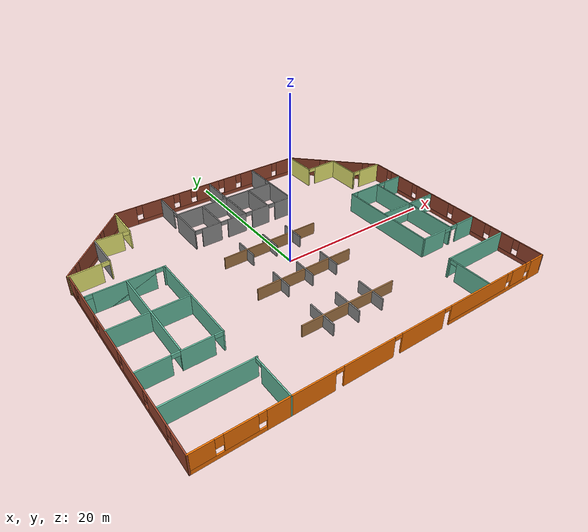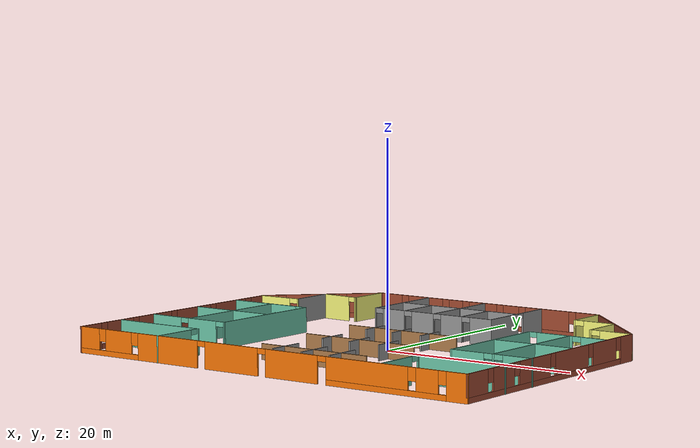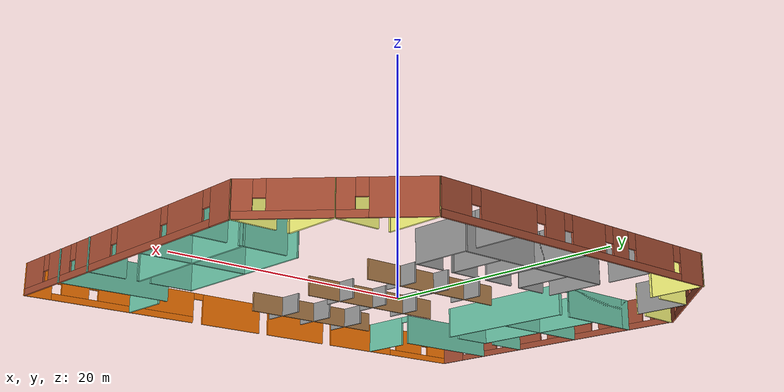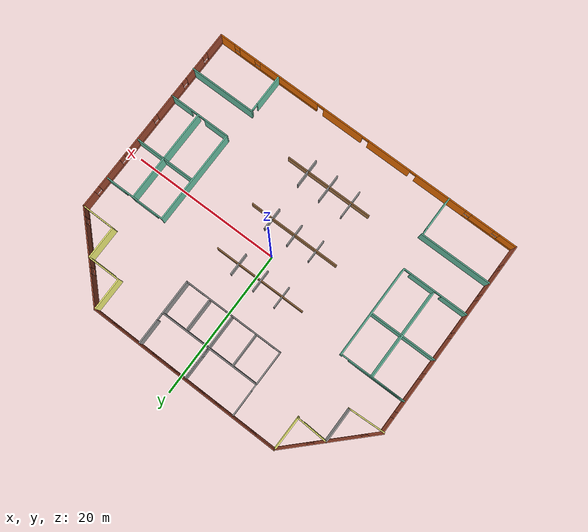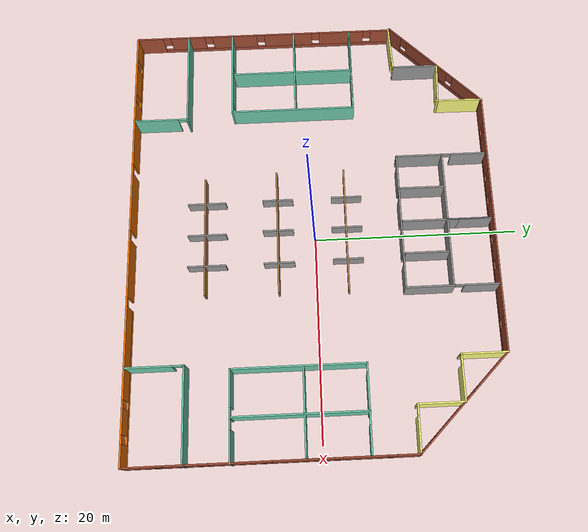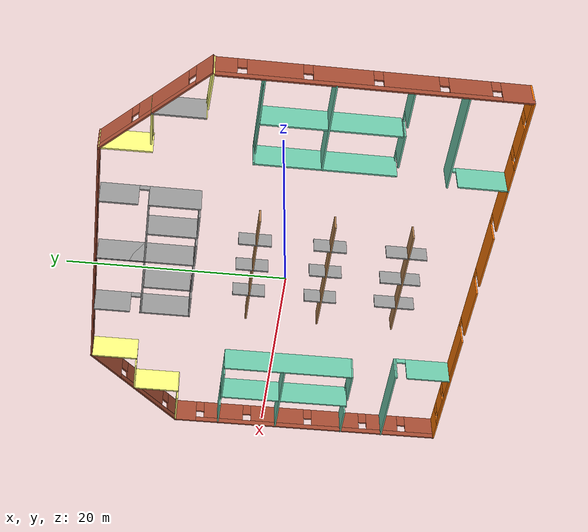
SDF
<?xml version='1.0'?>
<sdf version='1.6'>
  <model name='Building'>
    <pose frame=''>-0.640949 -0.136495 0 0 -0 0</pose>
    <link name='Wall_0'>
      <pose frame=''>-17.4265 13.2957 0 0 -0 0.785398</pose>
      <visual name='Wall_0_Visual_0'>
        <pose frame=''>-5.47881 0 1.25 0 -0 0</pose>
        <geometry>
          <box>
            <size>1.79239 0.15 2.5</size>
          </box>
        </geometry>
        <material>
          <script>
            <uri>file://media/materials/scripts/gazebo.material</uri>
            <name>Gazebo/Bricks</name>
          </script>
          <ambient>0.333333 0.666667 1 1</ambient>
        </material>
        <meta>
          <layer>0</layer>
        </meta>
      </visual>
      <collision name='Wall_0_Collision_0'>
        <geometry>
          <box>
            <size>1.79239 0.15 2.5</size>
          </box>
        </geometry>
        <pose frame=''>-5.47881 0 1.25 0 -0 0</pose>
      </collision>
      <visual name='Wall_0_Visual_1'>
        <pose frame=''>0.896194 0 0.25 0 -0 0</pose>
        <geometry>
          <box>
            <size>10.9576 0.15 0.5</size>
          </box>
        </geometry>
        <material>
          <script>
            <uri>file://media/materials/scripts/gazebo.material</uri>
            <name>Gazebo/Bricks</name>
          </script>
          <ambient>0.333333 0.666667 1 1</ambient>
        </material>
        <meta>
          <layer>0</layer>
        </meta>
      </visual>
      <collision name='Wall_0_Collision_1'>
        <geometry>
          <box>
            <size>10.9576 0.15 0.5</size>
          </box>
        </geometry>
        <pose frame=''>0.896194 0 0.25 0 -0 0</pose>
      </collision>
      <visual name='Wall_0_Visual_2'>
        <pose frame=''>-1.03961 0 1.5 0 -0 0</pose>
        <geometry>
          <box>
            <size>5.48599 0.15 2</size>
          </box>
        </geometry>
        <material>
          <script>
            <uri>file://media/materials/scripts/gazebo.material</uri>
            <name>Gazebo/Bricks</name>
          </script>
          <ambient>0.333333 0.666667 1 1</ambient>
        </material>
        <meta>
          <layer>0</layer>
        </meta>
      </visual>
      <collision name='Wall_0_Collision_2'>
        <geometry>
          <box>
            <size>5.48599 0.15 2</size>
          </box>
        </geometry>
        <pose frame=''>-1.03961 0 1.5 0 -0 0</pose>
      </collision>
      <visual name='Wall_0_Visual_3'>
        <pose frame=''>4.43919 0 1.5 0 -0 0</pose>
        <geometry>
          <box>
            <size>3.87162 0.15 2</size>
          </box>
        </geometry>
        <material>
          <script>
            <uri>file://media/materials/scripts/gazebo.material</uri>
            <name>Gazebo/Bricks</name>
          </script>
          <ambient>0.333333 0.666667 1 1</ambient>
        </material>
        <meta>
          <layer>0</layer>
        </meta>
      </visual>
      <collision name='Wall_0_Collision_3'>
        <geometry>
          <box>
            <size>3.87162 0.15 2</size>
          </box>
        </geometry>
        <pose frame=''>4.43919 0 1.5 0 -0 0</pose>
      </collision>
      <visual name='Wall_0_Visual_4'>
        <pose frame=''>-4.18261 0 1.9 0 -0 0</pose>
        <geometry>
          <box>
            <size>0.8 0.15 1.2</size>
          </box>
        </geometry>
        <material>
          <script>
            <uri>file://media/materials/scripts/gazebo.material</uri>
            <name>Gazebo/Bricks</name>
          </script>
          <ambient>0.333333 0.666667 1 1</ambient>
        </material>
        <meta>
          <layer>0</layer>
        </meta>
      </visual>
      <collision name='Wall_0_Collision_4'>
        <geometry>
          <box>
            <size>0.8 0.15 1.2</size>
          </box>
        </geometry>
        <pose frame=''>-4.18261 0 1.9 0 -0 0</pose>
      </collision>
      <visual name='Wall_0_Visual_5'>
        <pose frame=''>2.10338 0 1.9 0 -0 0</pose>
        <geometry>
          <box>
            <size>0.8 0.15 1.2</size>
          </box>
        </geometry>
        <material>
          <script>
            <uri>file://media/materials/scripts/gazebo.material</uri>
            <name>Gazebo/Bricks</name>
          </script>
          <ambient>0.333333 0.666667 1 1</ambient>
        </material>
        <meta>
          <layer>0</layer>
        </meta>
      </visual>
      <collision name='Wall_0_Collision_5'>
        <geometry>
          <box>
            <size>0.8 0.15 1.2</size>
          </box>
        </geometry>
        <pose frame=''>2.10338 0 1.9 0 -0 0</pose>
      </collision>
    </link>
    <link name='Wall_1'>
      <pose frame=''>0.031457 17.6569 0 0 0 -0.007145</pose>
      <visual name='Wall_1_Visual_0'>
        <pose frame=''>-11.7992 0 1.25 0 -0 0</pose>
        <geometry>
          <box>
            <size>2.74584 0.15 2.5</size>
          </box>
        </geometry>
        <material>
          <script>
            <uri>file://media/materials/scripts/gazebo.material</uri>
            <name>Gazebo/Bricks</name>
          </script>
          <ambient>0.333333 0.666667 1 1</ambient>
        </material>
        <meta>
          <layer>0</layer>
        </meta>
      </visual>
      <collision name='Wall_1_Collision_0'>
        <geometry>
          <box>
            <size>2.74584 0.15 2.5</size>
          </box>
        </geometry>
        <pose frame=''>-11.7992 0 1.25 0 -0 0</pose>
      </collision>
      <visual name='Wall_1_Visual_1'>
        <pose frame=''>1.37292 0 0.25 0 -0 0</pose>
        <geometry>
          <box>
            <size>23.5984 0.15 0.5</size>
          </box>
        </geometry>
        <material>
          <script>
            <uri>file://media/materials/scripts/gazebo.material</uri>
            <name>Gazebo/Bricks</name>
          </script>
          <ambient>0.333333 0.666667 1 1</ambient>
        </material>
        <meta>
          <layer>0</layer>
        </meta>
      </visual>
      <collision name='Wall_1_Collision_1'>
        <geometry>
          <box>
            <size>23.5984 0.15 0.5</size>
          </box>
        </geometry>
        <pose frame=''>1.37292 0 0.25 0 -0 0</pose>
      </collision>
      <visual name='Wall_1_Visual_2'>
        <pose frame=''>-7.47171 0 1.5 0 -0 0</pose>
        <geometry>
          <box>
            <size>4.30914 0.15 2</size>
          </box>
        </geometry>
        <material>
          <script>
            <uri>file://media/materials/scripts/gazebo.material</uri>
            <name>Gazebo/Bricks</name>
          </script>
          <ambient>0.333333 0.666667 1 1</ambient>
        </material>
        <meta>
          <layer>0</layer>
        </meta>
      </visual>
      <collision name='Wall_1_Collision_2'>
        <geometry>
          <box>
            <size>4.30914 0.15 2</size>
          </box>
        </geometry>
        <pose frame=''>-7.47171 0 1.5 0 -0 0</pose>
      </collision>
      <visual name='Wall_1_Visual_3'>
        <pose frame=''>-3.69187 0 1.5 0 -0 0</pose>
        <geometry>
          <box>
            <size>1.65055 0.15 2</size>
          </box>
        </geometry>
        <material>
          <script>
            <uri>file://media/materials/scripts/gazebo.material</uri>
            <name>Gazebo/Bricks</name>
          </script>
          <ambient>0.333333 0.666667 1 1</ambient>
        </material>
        <meta>
          <layer>0</layer>
        </meta>
      </visual>
      <collision name='Wall_1_Collision_3'>
        <geometry>
          <box>
            <size>1.65055 0.15 2</size>
          </box>
        </geometry>
        <pose frame=''>-3.69187 0 1.5 0 -0 0</pose>
      </collision>
      <visual name='Wall_1_Visual_4'>
        <pose frame=''>-0.393041 0 1.5 0 -0 0</pose>
        <geometry>
          <box>
            <size>3.3471 0.15 2</size>
          </box>
        </geometry>
        <material>
          <script>
            <uri>file://media/materials/scripts/gazebo.material</uri>
            <name>Gazebo/Bricks</name>
          </script>
          <ambient>0.333333 0.666667 1 1</ambient>
        </material>
        <meta>
          <layer>0</layer>
        </meta>
      </visual>
      <collision name='Wall_1_Collision_4'>
        <geometry>
          <box>
            <size>3.3471 0.15 2</size>
          </box>
        </geometry>
        <pose frame=''>-0.393041 0 1.5 0 -0 0</pose>
      </collision>
      <visual name='Wall_1_Visual_5'>
        <pose frame=''>3.00004 0 1.5 0 -0 0</pose>
        <geometry>
          <box>
            <size>1.83906 0.15 2</size>
          </box>
        </geometry>
        <material>
          <script>
            <uri>file://media/materials/scripts/gazebo.material</uri>
            <name>Gazebo/Bricks</name>
          </script>
          <ambient>0.333333 0.666667 1 1</ambient>
        </material>
        <meta>
          <layer>0</layer>
        </meta>
      </visual>
      <collision name='Wall_1_Collision_5'>
        <geometry>
          <box>
            <size>1.83906 0.15 2</size>
          </box>
        </geometry>
        <pose frame=''>3.00004 0 1.5 0 -0 0</pose>
      </collision>
      <visual name='Wall_1_Visual_6'>
        <pose frame=''>7.23663 0 1.5 0 -0 0</pose>
        <geometry>
          <box>
            <size>5.03413 0.15 2</size>
          </box>
        </geometry>
        <material>
          <script>
            <uri>file://media/materials/scripts/gazebo.material</uri>
            <name>Gazebo/Bricks</name>
          </script>
          <ambient>0.333333 0.666667 1 1</ambient>
        </material>
        <meta>
          <layer>0</layer>
        </meta>
      </visual>
      <collision name='Wall_1_Collision_6'>
        <geometry>
          <box>
            <size>5.03413 0.15 2</size>
          </box>
        </geometry>
        <pose frame=''>7.23663 0 1.5 0 -0 0</pose>
      </collision>
      <visual name='Wall_1_Visual_7'>
        <pose frame=''>11.8629 0 1.5 0 -0 0</pose>
        <geometry>
          <box>
            <size>2.61843 0.15 2</size>
          </box>
        </geometry>
        <material>
          <script>
            <uri>file://media/materials/scripts/gazebo.material</uri>
            <name>Gazebo/Bricks</name>
          </script>
          <ambient>0.333333 0.666667 1 1</ambient>
        </material>
        <meta>
          <layer>0</layer>
        </meta>
      </visual>
      <collision name='Wall_1_Collision_7'>
        <geometry>
          <box>
            <size>2.61843 0.15 2</size>
          </box>
        </geometry>
        <pose frame=''>11.8629 0 1.5 0 -0 0</pose>
      </collision>
      <visual name='Wall_1_Visual_8'>
        <pose frame=''>-10.0263 0 1.9 0 -0 0</pose>
        <geometry>
          <box>
            <size>0.8 0.15 1.2</size>
          </box>
        </geometry>
        <material>
          <script>
            <uri>file://media/materials/scripts/gazebo.material</uri>
            <name>Gazebo/Bricks</name>
          </script>
          <ambient>0.333333 0.666667 1 1</ambient>
        </material>
        <meta>
          <layer>0</layer>
        </meta>
      </visual>
      <collision name='Wall_1_Collision_8'>
        <geometry>
          <box>
            <size>0.8 0.15 1.2</size>
          </box>
        </geometry>
        <pose frame=''>-10.0263 0 1.9 0 -0 0</pose>
      </collision>
      <visual name='Wall_1_Visual_9'>
        <pose frame=''>-4.91714 0 1.9 0 -0 0</pose>
        <geometry>
          <box>
            <size>0.8 0.15 1.2</size>
          </box>
        </geometry>
        <material>
          <script>
            <uri>file://media/materials/scripts/gazebo.material</uri>
            <name>Gazebo/Bricks</name>
          </script>
          <ambient>0.333333 0.666667 1 1</ambient>
        </material>
        <meta>
          <layer>0</layer>
        </meta>
      </visual>
      <collision name='Wall_1_Collision_9'>
        <geometry>
          <box>
            <size>0.8 0.15 1.2</size>
          </box>
        </geometry>
        <pose frame=''>-4.91714 0 1.9 0 -0 0</pose>
      </collision>
      <visual name='Wall_1_Visual_10'>
        <pose frame=''>-2.46659 0 1.9 0 -0 0</pose>
        <geometry>
          <box>
            <size>0.8 0.15 1.2</size>
          </box>
        </geometry>
        <material>
          <script>
            <uri>file://media/materials/scripts/gazebo.material</uri>
            <name>Gazebo/Bricks</name>
          </script>
          <ambient>0.333333 0.666667 1 1</ambient>
        </material>
        <meta>
          <layer>0</layer>
        </meta>
      </visual>
      <collision name='Wall_1_Collision_10'>
        <geometry>
          <box>
            <size>0.8 0.15 1.2</size>
          </box>
        </geometry>
        <pose frame=''>-2.46659 0 1.9 0 -0 0</pose>
      </collision>
      <visual name='Wall_1_Visual_11'>
        <pose frame=''>1.68051 0 1.9 0 -0 0</pose>
        <geometry>
          <box>
            <size>0.8 0.15 1.2</size>
          </box>
        </geometry>
        <material>
          <script>
            <uri>file://media/materials/scripts/gazebo.material</uri>
            <name>Gazebo/Bricks</name>
          </script>
          <ambient>0.333333 0.666667 1 1</ambient>
        </material>
        <meta>
          <layer>0</layer>
        </meta>
      </visual>
      <collision name='Wall_1_Collision_11'>
        <geometry>
          <box>
            <size>0.8 0.15 1.2</size>
          </box>
        </geometry>
        <pose frame=''>1.68051 0 1.9 0 -0 0</pose>
      </collision>
      <visual name='Wall_1_Visual_12'>
        <pose frame=''>4.31956 0 1.9 0 -0 0</pose>
        <geometry>
          <box>
            <size>0.8 0.15 1.2</size>
          </box>
        </geometry>
        <material>
          <script>
            <uri>file://media/materials/scripts/gazebo.material</uri>
            <name>Gazebo/Bricks</name>
          </script>
          <ambient>0.333333 0.666667 1 1</ambient>
        </material>
        <meta>
          <layer>0</layer>
        </meta>
      </visual>
      <collision name='Wall_1_Collision_12'>
        <geometry>
          <box>
            <size>0.8 0.15 1.2</size>
          </box>
        </geometry>
        <pose frame=''>4.31956 0 1.9 0 -0 0</pose>
      </collision>
      <visual name='Wall_1_Visual_13'>
        <pose frame=''>10.1537 0 1.9 0 -0 0</pose>
        <geometry>
          <box>
            <size>0.8 0.15 1.2</size>
          </box>
        </geometry>
        <material>
          <script>
            <uri>file://media/materials/scripts/gazebo.material</uri>
            <name>Gazebo/Bricks</name>
          </script>
          <ambient>0.333333 0.666667 1 1</ambient>
        </material>
        <meta>
          <layer>0</layer>
        </meta>
      </visual>
      <collision name='Wall_1_Collision_13'>
        <geometry>
          <box>
            <size>0.8 0.15 1.2</size>
          </box>
        </geometry>
        <pose frame=''>10.1537 0 1.9 0 -0 0</pose>
      </collision>
    </link>
    <link name='Wall_15'>
      <pose frame=''>-12.1249 -15.1066 0 0 0 -1.5708</pose>
      <visual name='Wall_15_Visual_0'>
        <pose frame=''>-2.71892 0 1.25 0 -0 0</pose>
        <geometry>
          <box>
            <size>0.062153 0.15 2.5</size>
          </box>
        </geometry>
        <material>
          <script>
            <uri>file://media/materials/scripts/gazebo.material</uri>
            <name>Gazebo/Grey</name>
          </script>
          <ambient>0.435294 0.796078 0.67451 1</ambient>
        </material>
        <meta>
          <layer>0</layer>
        </meta>
      </visual>
      <collision name='Wall_15_Collision_0'>
        <geometry>
          <box>
            <size>0.062153 0.15 2.5</size>
          </box>
        </geometry>
        <pose frame=''>-2.71892 0 1.25 0 -0 0</pose>
      </collision>
      <visual name='Wall_15_Visual_1'>
        <pose frame=''>0.481076 0 1.25 0 -0 0</pose>
        <geometry>
          <box>
            <size>4.53785 0.15 2.5</size>
          </box>
        </geometry>
        <material>
          <script>
            <uri>file://media/materials/scripts/gazebo.material</uri>
            <name>Gazebo/Grey</name>
          </script>
          <ambient>0.435294 0.796078 0.67451 1</ambient>
        </material>
        <meta>
          <layer>0</layer>
        </meta>
      </visual>
      <collision name='Wall_15_Collision_1'>
        <geometry>
          <box>
            <size>4.53785 0.15 2.5</size>
          </box>
        </geometry>
        <pose frame=''>0.481076 0 1.25 0 -0 0</pose>
      </collision>
      <visual name='Wall_15_Visual_2'>
        <pose frame=''>-2.23785 0 2.25 0 -0 0</pose>
        <geometry>
          <box>
            <size>0.9 0.15 0.5</size>
          </box>
        </geometry>
        <material>
          <script>
            <uri>file://media/materials/scripts/gazebo.material</uri>
            <name>Gazebo/Grey</name>
          </script>
          <ambient>0.435294 0.796078 0.67451 1</ambient>
        </material>
        <meta>
          <layer>0</layer>
        </meta>
      </visual>
      <collision name='Wall_15_Collision_2'>
        <geometry>
          <box>
            <size>0.9 0.15 0.5</size>
          </box>
        </geometry>
        <pose frame=''>-2.23785 0 2.25 0 -0 0</pose>
      </collision>
    </link>
    <link name='Wall_17'>
      <collision name='Wall_17_Collision'>
        <geometry>
          <box>
            <size>9 0.15 2.5</size>
          </box>
        </geometry>
        <pose frame=''>0 0 1.25 0 -0 0</pose>
      </collision>
      <visual name='Wall_17_Visual'>
        <pose frame=''>0 0 1.25 0 -0 0</pose>
        <geometry>
          <box>
            <size>9 0.15 2.5</size>
          </box>
        </geometry>
        <material>
          <script>
            <uri>file://media/materials/scripts/gazebo.material</uri>
            <name>Gazebo/Grey</name>
          </script>
          <ambient>0.435294 0.796078 0.67451 1</ambient>
        </material>
        <meta>
          <layer>0</layer>
        </meta>
      </visual>
      <pose frame=''>17.4874 -12.3073 0 0 -0 3.14159</pose>
    </link>
    <link name='Wall_18'>
      <pose frame=''>13.0624 -14.9823 0 0 0 -1.5708</pose>
      <visual name='Wall_18_Visual_0'>
        <pose frame=''>-2.60998 0 1.25 0 -0 0</pose>
        <geometry>
          <box>
            <size>0.280034 0.15 2.5</size>
          </box>
        </geometry>
        <material>
          <script>
            <uri>file://media/materials/scripts/gazebo.material</uri>
            <name>Gazebo/Grey</name>
          </script>
          <ambient>0.435294 0.796078 0.67451 1</ambient>
        </material>
        <meta>
          <layer>0</layer>
        </meta>
      </visual>
      <collision name='Wall_18_Collision_0'>
        <geometry>
          <box>
            <size>0.280034 0.15 2.5</size>
          </box>
        </geometry>
        <pose frame=''>-2.60998 0 1.25 0 -0 0</pose>
      </collision>
      <visual name='Wall_18_Visual_1'>
        <pose frame=''>0.590017 0 1.25 0 -0 0</pose>
        <geometry>
          <box>
            <size>4.31997 0.15 2.5</size>
          </box>
        </geometry>
        <material>
          <script>
            <uri>file://media/materials/scripts/gazebo.material</uri>
            <name>Gazebo/Grey</name>
          </script>
          <ambient>0.435294 0.796078 0.67451 1</ambient>
        </material>
        <meta>
          <layer>0</layer>
        </meta>
      </visual>
      <collision name='Wall_18_Collision_1'>
        <geometry>
          <box>
            <size>4.31997 0.15 2.5</size>
          </box>
        </geometry>
        <pose frame=''>0.590017 0 1.25 0 -0 0</pose>
      </collision>
      <visual name='Wall_18_Visual_2'>
        <pose frame=''>-2.01997 0 2.25 0 -0 0</pose>
        <geometry>
          <box>
            <size>0.9 0.15 0.5</size>
          </box>
        </geometry>
        <material>
          <script>
            <uri>file://media/materials/scripts/gazebo.material</uri>
            <name>Gazebo/Grey</name>
          </script>
          <ambient>0.435294 0.796078 0.67451 1</ambient>
        </material>
        <meta>
          <layer>0</layer>
        </meta>
      </visual>
      <collision name='Wall_18_Collision_2'>
        <geometry>
          <box>
            <size>0.9 0.15 0.5</size>
          </box>
        </geometry>
        <pose frame=''>-2.01997 0 2.25 0 -0 0</pose>
      </collision>
    </link>
    <link name='Wall_2'>
      <pose frame=''>17.4946 13.197 0 0 0 -0.785398</pose>
      <visual name='Wall_2_Visual_0'>
        <pose frame=''>-4.12695 0 1.25 0 -0 0</pose>
        <geometry>
          <box>
            <size>4.24611 0.15 2.5</size>
          </box>
        </geometry>
        <material>
          <script>
            <uri>file://media/materials/scripts/gazebo.material</uri>
            <name>Gazebo/Bricks</name>
          </script>
          <ambient>0.333333 0.666667 1 1</ambient>
        </material>
        <meta>
          <layer>0</layer>
        </meta>
      </visual>
      <collision name='Wall_2_Collision_0'>
        <geometry>
          <box>
            <size>4.24611 0.15 2.5</size>
          </box>
        </geometry>
        <pose frame=''>-4.12695 0 1.25 0 -0 0</pose>
      </collision>
      <visual name='Wall_2_Visual_1'>
        <pose frame=''>2.12305 0 0.25 0 -0 0</pose>
        <geometry>
          <box>
            <size>8.25389 0.15 0.5</size>
          </box>
        </geometry>
        <material>
          <script>
            <uri>file://media/materials/scripts/gazebo.material</uri>
            <name>Gazebo/Bricks</name>
          </script>
          <ambient>0.333333 0.666667 1 1</ambient>
        </material>
        <meta>
          <layer>0</layer>
        </meta>
      </visual>
      <collision name='Wall_2_Collision_1'>
        <geometry>
          <box>
            <size>8.25389 0.15 0.5</size>
          </box>
        </geometry>
        <pose frame=''>2.12305 0 0.25 0 -0 0</pose>
      </collision>
      <visual name='Wall_2_Visual_2'>
        <pose frame=''>1.43985 0 1.5 0 -0 0</pose>
        <geometry>
          <box>
            <size>5.28749 0.15 2</size>
          </box>
        </geometry>
        <material>
          <script>
            <uri>file://media/materials/scripts/gazebo.material</uri>
            <name>Gazebo/Bricks</name>
          </script>
          <ambient>0.333333 0.666667 1 1</ambient>
        </material>
        <meta>
          <layer>0</layer>
        </meta>
      </visual>
      <collision name='Wall_2_Collision_2'>
        <geometry>
          <box>
            <size>5.28749 0.15 2</size>
          </box>
        </geometry>
        <pose frame=''>1.43985 0 1.5 0 -0 0</pose>
      </collision>
      <visual name='Wall_2_Visual_3'>
        <pose frame=''>5.5668 0 1.5 0 -0 0</pose>
        <geometry>
          <box>
            <size>1.3664 0.15 2</size>
          </box>
        </geometry>
        <material>
          <script>
            <uri>file://media/materials/scripts/gazebo.material</uri>
            <name>Gazebo/Bricks</name>
          </script>
          <ambient>0.333333 0.666667 1 1</ambient>
        </material>
        <meta>
          <layer>0</layer>
        </meta>
      </visual>
      <collision name='Wall_2_Collision_3'>
        <geometry>
          <box>
            <size>1.3664 0.15 2</size>
          </box>
        </geometry>
        <pose frame=''>5.5668 0 1.5 0 -0 0</pose>
      </collision>
      <visual name='Wall_2_Visual_4'>
        <pose frame=''>-1.60389 0 1.9 0 -0 0</pose>
        <geometry>
          <box>
            <size>0.8 0.15 1.2</size>
          </box>
        </geometry>
        <material>
          <script>
            <uri>file://media/materials/scripts/gazebo.material</uri>
            <name>Gazebo/Bricks</name>
          </script>
          <ambient>0.333333 0.666667 1 1</ambient>
        </material>
        <meta>
          <layer>0</layer>
        </meta>
      </visual>
      <collision name='Wall_2_Collision_4'>
        <geometry>
          <box>
            <size>0.8 0.15 1.2</size>
          </box>
        </geometry>
        <pose frame=''>-1.60389 0 1.9 0 -0 0</pose>
      </collision>
      <visual name='Wall_2_Visual_5'>
        <pose frame=''>4.4836 0 1.9 0 -0 0</pose>
        <geometry>
          <box>
            <size>0.8 0.15 1.2</size>
          </box>
        </geometry>
        <material>
          <script>
            <uri>file://media/materials/scripts/gazebo.material</uri>
            <name>Gazebo/Bricks</name>
          </script>
          <ambient>0.333333 0.666667 1 1</ambient>
        </material>
        <meta>
          <layer>0</layer>
        </meta>
      </visual>
      <collision name='Wall_2_Collision_5'>
        <geometry>
          <box>
            <size>0.8 0.15 1.2</size>
          </box>
        </geometry>
        <pose frame=''>4.4836 0 1.9 0 -0 0</pose>
      </collision>
    </link>
    <link name='Wall_20'>
      <collision name='Wall_20_Collision'>
        <geometry>
          <box>
            <size>4.68741 0.15 2.5</size>
          </box>
        </geometry>
        <pose frame=''>0 0 1.25 0 -0 0</pose>
      </collision>
      <visual name='Wall_20_Visual'>
        <pose frame=''>0 0 1.25 0 -0 0</pose>
        <geometry>
          <box>
            <size>4.68741 0.15 2.5</size>
          </box>
        </geometry>
        <material>
          <script>
            <uri>file://media/materials/scripts/gazebo.material</uri>
            <name>Gazebo/Grey</name>
          </script>
          <ambient>1 1 0.498039 1</ambient>
        </material>
        <meta>
          <layer>0</layer>
        </meta>
      </visual>
      <pose frame=''>-13.0893 15.4819 0 0 0 -1.58136</pose>
    </link>
    <link name='Wall_21'>
      <pose frame=''>-15.1633 13.3917 0 0 -0 3.08915</pose>
      <visual name='Wall_21_Visual_0'>
        <pose frame=''>-2.118 0 1.25 0 -0 0</pose>
        <geometry>
          <box>
            <size>0.019653 0.15 2.5</size>
          </box>
        </geometry>
        <material>
          <script>
            <uri>file://media/materials/scripts/gazebo.material</uri>
            <name>Gazebo/Grey</name>
          </script>
          <ambient>1 1 0.498039 1</ambient>
        </material>
        <meta>
          <layer>0</layer>
        </meta>
      </visual>
      <collision name='Wall_21_Collision_0'>
        <geometry>
          <box>
            <size>0.019653 0.15 2.5</size>
          </box>
        </geometry>
        <pose frame=''>-2.118 0 1.25 0 -0 0</pose>
      </collision>
      <visual name='Wall_21_Visual_1'>
        <pose frame=''>0.459827 0 1.25 0 -0 0</pose>
        <geometry>
          <box>
            <size>3.33599 0.15 2.5</size>
          </box>
        </geometry>
        <material>
          <script>
            <uri>file://media/materials/scripts/gazebo.material</uri>
            <name>Gazebo/Grey</name>
          </script>
          <ambient>1 1 0.498039 1</ambient>
        </material>
        <meta>
          <layer>0</layer>
        </meta>
      </visual>
      <collision name='Wall_21_Collision_1'>
        <geometry>
          <box>
            <size>3.33599 0.15 2.5</size>
          </box>
        </geometry>
        <pose frame=''>0.459827 0 1.25 0 -0 0</pose>
      </collision>
      <visual name='Wall_21_Visual_2'>
        <pose frame=''>-1.65817 0 2.25 0 -0 0</pose>
        <geometry>
          <box>
            <size>0.9 0.15 0.5</size>
          </box>
        </geometry>
        <material>
          <script>
            <uri>file://media/materials/scripts/gazebo.material</uri>
            <name>Gazebo/Grey</name>
          </script>
          <ambient>1 1 0.498039 1</ambient>
        </material>
        <meta>
          <layer>0</layer>
        </meta>
      </visual>
      <collision name='Wall_21_Collision_2'>
        <geometry>
          <box>
            <size>0.9 0.15 0.5</size>
          </box>
        </geometry>
        <pose frame=''>-1.65817 0 2.25 0 -0 0</pose>
      </collision>
    </link>
    <link name='Wall_22'>
      <collision name='Wall_22_Collision'>
        <geometry>
          <box>
            <size>4.57076 0.15 2.5</size>
          </box>
        </geometry>
        <pose frame=''>0 0 1.25 0 -0 0</pose>
      </collision>
      <visual name='Wall_22_Visual'>
        <pose frame=''>0 0 1.25 0 -0 0</pose>
        <geometry>
          <box>
            <size>4.57076 0.15 2.5</size>
          </box>
        </geometry>
        <material>
          <script>
            <uri>file://media/materials/scripts/gazebo.material</uri>
            <name>Gazebo/Grey</name>
          </script>
          <ambient>1 1 1 1</ambient>
        </material>
        <meta>
          <layer>0</layer>
        </meta>
      </visual>
      <pose frame=''>-17.2133 11.2182 0 0 0 -1.5708</pose>
    </link>
    <link name='Wall_23'>
      <pose frame=''>-19.5133 8.82945 0 0 0 -3.09484</pose>
      <visual name='Wall_23_Visual_0'>
        <pose frame=''>-2.31222 0 1.25 0 -0 0</pose>
        <geometry>
          <box>
            <size>0.130592 0.15 2.5</size>
          </box>
        </geometry>
        <material>
          <script>
            <uri>file://media/materials/scripts/gazebo.material</uri>
            <name>Gazebo/Grey</name>
          </script>
          <ambient>1 1 0.498039 1</ambient>
        </material>
        <meta>
          <layer>0</layer>
        </meta>
      </visual>
      <collision name='Wall_23_Collision_0'>
        <geometry>
          <box>
            <size>0.130592 0.15 2.5</size>
          </box>
        </geometry>
        <pose frame=''>-2.31222 0 1.25 0 -0 0</pose>
      </collision>
      <visual name='Wall_23_Visual_1'>
        <pose frame=''>0.515296 0 1.25 0 -0 0</pose>
        <geometry>
          <box>
            <size>3.72444 0.15 2.5</size>
          </box>
        </geometry>
        <material>
          <script>
            <uri>file://media/materials/scripts/gazebo.material</uri>
            <name>Gazebo/Grey</name>
          </script>
          <ambient>1 1 0.498039 1</ambient>
        </material>
        <meta>
          <layer>0</layer>
        </meta>
      </visual>
      <collision name='Wall_23_Collision_1'>
        <geometry>
          <box>
            <size>3.72444 0.15 2.5</size>
          </box>
        </geometry>
        <pose frame=''>0.515296 0 1.25 0 -0 0</pose>
      </collision>
      <visual name='Wall_23_Visual_2'>
        <pose frame=''>-1.79692 0 2.25 0 -0 0</pose>
        <geometry>
          <box>
            <size>0.9 0.15 0.5</size>
          </box>
        </geometry>
        <material>
          <script>
            <uri>file://media/materials/scripts/gazebo.material</uri>
            <name>Gazebo/Grey</name>
          </script>
          <ambient>1 1 0.498039 1</ambient>
        </material>
        <meta>
          <layer>0</layer>
        </meta>
      </visual>
      <collision name='Wall_23_Collision_2'>
        <geometry>
          <box>
            <size>0.9 0.15 0.5</size>
          </box>
        </geometry>
        <pose frame=''>-1.79692 0 2.25 0 -0 0</pose>
      </collision>
    </link>
    <link name='Wall_25'>
      <collision name='Wall_25_Collision'>
        <geometry>
          <box>
            <size>4.5 0.15 2.5</size>
          </box>
        </geometry>
        <pose frame=''>0 0 1.25 0 -0 0</pose>
      </collision>
      <visual name='Wall_25_Visual'>
        <pose frame=''>0 0 1.25 0 -0 0</pose>
        <geometry>
          <box>
            <size>4.5 0.15 2.5</size>
          </box>
        </geometry>
        <material>
          <script>
            <uri>file://media/materials/scripts/gazebo.material</uri>
            <name>Gazebo/Grey</name>
          </script>
          <ambient>1 1 0.498039 1</ambient>
        </material>
        <meta>
          <layer>0</layer>
        </meta>
      </visual>
      <pose frame=''>13.1282 15.3884 0 0 0 -1.5708</pose>
    </link>
    <link name='Wall_26'>
      <pose frame=''>15.3032 13.2134 0 0 -0 0</pose>
      <visual name='Wall_26_Visual_0'>
        <pose frame=''>-2.16279 0 1.25 0 -0 0</pose>
        <geometry>
          <box>
            <size>0.174413 0.15 2.5</size>
          </box>
        </geometry>
        <material>
          <script>
            <uri>file://media/materials/scripts/gazebo.material</uri>
            <name>Gazebo/Grey</name>
          </script>
          <ambient>1 1 0.498039 1</ambient>
        </material>
        <meta>
          <layer>0</layer>
        </meta>
      </visual>
      <collision name='Wall_26_Collision_0'>
        <geometry>
          <box>
            <size>0.174413 0.15 2.5</size>
          </box>
        </geometry>
        <pose frame=''>-2.16279 0 1.25 0 -0 0</pose>
      </collision>
      <visual name='Wall_26_Visual_1'>
        <pose frame=''>0.537207 0 1.25 0 -0 0</pose>
        <geometry>
          <box>
            <size>3.42559 0.15 2.5</size>
          </box>
        </geometry>
        <material>
          <script>
            <uri>file://media/materials/scripts/gazebo.material</uri>
            <name>Gazebo/Grey</name>
          </script>
          <ambient>1 1 0.498039 1</ambient>
        </material>
        <meta>
          <layer>0</layer>
        </meta>
      </visual>
      <collision name='Wall_26_Collision_1'>
        <geometry>
          <box>
            <size>3.42559 0.15 2.5</size>
          </box>
        </geometry>
        <pose frame=''>0.537207 0 1.25 0 -0 0</pose>
      </collision>
      <visual name='Wall_26_Visual_2'>
        <pose frame=''>-1.62559 0 2.25 0 -0 0</pose>
        <geometry>
          <box>
            <size>0.9 0.15 0.5</size>
          </box>
        </geometry>
        <material>
          <script>
            <uri>file://media/materials/scripts/gazebo.material</uri>
            <name>Gazebo/Grey</name>
          </script>
          <ambient>1 1 0.498039 1</ambient>
        </material>
        <meta>
          <layer>0</layer>
        </meta>
      </visual>
      <collision name='Wall_26_Collision_2'>
        <geometry>
          <box>
            <size>0.9 0.15 0.5</size>
          </box>
        </geometry>
        <pose frame=''>-1.62559 0 2.25 0 -0 0</pose>
      </collision>
    </link>
    <link name='Wall_27'>
      <collision name='Wall_27_Collision'>
        <geometry>
          <box>
            <size>4.5 0.15 2.5</size>
          </box>
        </geometry>
        <pose frame=''>0 0 1.25 0 -0 0</pose>
      </collision>
      <visual name='Wall_27_Visual'>
        <pose frame=''>0 0 1.25 0 -0 0</pose>
        <geometry>
          <box>
            <size>4.5 0.15 2.5</size>
          </box>
        </geometry>
        <material>
          <script>
            <uri>file://media/materials/scripts/gazebo.material</uri>
            <name>Gazebo/Grey</name>
          </script>
          <ambient>1 1 0.498039 1</ambient>
        </material>
        <meta>
          <layer>0</layer>
        </meta>
      </visual>
      <pose frame=''>17.4782 11.0384 0 0 0 -1.5708</pose>
    </link>
    <link name='Wall_28'>
      <pose frame=''>19.6696 8.84697 0 0 0 -0.007477</pose>
      <visual name='Wall_28_Visual_0'>
        <pose frame=''>-2.15512 0 1.25 0 -0 0</pose>
        <geometry>
          <box>
            <size>0.222645 0.15 2.5</size>
          </box>
        </geometry>
        <material>
          <script>
            <uri>file://media/materials/scripts/gazebo.material</uri>
            <name>Gazebo/Grey</name>
          </script>
          <ambient>1 1 0.498039 1</ambient>
        </material>
        <meta>
          <layer>0</layer>
        </meta>
      </visual>
      <collision name='Wall_28_Collision_0'>
        <geometry>
          <box>
            <size>0.222645 0.15 2.5</size>
          </box>
        </geometry>
        <pose frame=''>-2.15512 0 1.25 0 -0 0</pose>
      </collision>
      <visual name='Wall_28_Visual_1'>
        <pose frame=''>0.561323 0 1.25 0 -0 0</pose>
        <geometry>
          <box>
            <size>3.41025 0.15 2.5</size>
          </box>
        </geometry>
        <material>
          <script>
            <uri>file://media/materials/scripts/gazebo.material</uri>
            <name>Gazebo/Grey</name>
          </script>
          <ambient>1 1 0.498039 1</ambient>
        </material>
        <meta>
          <layer>0</layer>
        </meta>
      </visual>
      <collision name='Wall_28_Collision_1'>
        <geometry>
          <box>
            <size>3.41025 0.15 2.5</size>
          </box>
        </geometry>
        <pose frame=''>0.561323 0 1.25 0 -0 0</pose>
      </collision>
      <visual name='Wall_28_Visual_2'>
        <pose frame=''>-1.5938 0 2.25 0 -0 0</pose>
        <geometry>
          <box>
            <size>0.9 0.15 0.5</size>
          </box>
        </geometry>
        <material>
          <script>
            <uri>file://media/materials/scripts/gazebo.material</uri>
            <name>Gazebo/Grey</name>
          </script>
          <ambient>1 1 0.498039 1</ambient>
        </material>
        <meta>
          <layer>0</layer>
        </meta>
      </visual>
      <collision name='Wall_28_Collision_2'>
        <geometry>
          <box>
            <size>0.9 0.15 0.5</size>
          </box>
        </geometry>
        <pose frame=''>-1.5938 0 2.25 0 -0 0</pose>
      </collision>
    </link>
    <link name='Wall_3'>
      <pose frame=''>21.861 -4.46942 0 0 0 -1.5708</pose>
      <visual name='Wall_3_Visual_0'>
        <pose frame=''>-12.2912 0 1.25 0 -0 0</pose>
        <geometry>
          <box>
            <size>2.16764 0.15 2.5</size>
          </box>
        </geometry>
        <material>
          <script>
            <uri>file://media/materials/scripts/gazebo.material</uri>
            <name>Gazebo/Bricks</name>
          </script>
          <ambient>0.333333 0.666667 1 1</ambient>
        </material>
        <meta>
          <layer>0</layer>
        </meta>
      </visual>
      <collision name='Wall_3_Collision_0'>
        <geometry>
          <box>
            <size>2.16764 0.15 2.5</size>
          </box>
        </geometry>
        <pose frame=''>-12.2912 0 1.25 0 -0 0</pose>
      </collision>
      <visual name='Wall_3_Visual_1'>
        <pose frame=''>1.08382 0 0.25 0 -0 0</pose>
        <geometry>
          <box>
            <size>24.5824 0.15 0.5</size>
          </box>
        </geometry>
        <material>
          <script>
            <uri>file://media/materials/scripts/gazebo.material</uri>
            <name>Gazebo/Bricks</name>
          </script>
          <ambient>0.333333 0.666667 1 1</ambient>
        </material>
        <meta>
          <layer>0</layer>
        </meta>
      </visual>
      <collision name='Wall_3_Collision_1'>
        <geometry>
          <box>
            <size>24.5824 0.15 0.5</size>
          </box>
        </geometry>
        <pose frame=''>1.08382 0 0.25 0 -0 0</pose>
      </collision>
      <visual name='Wall_3_Visual_2'>
        <pose frame=''>-8.40981 0 1.5 0 -0 0</pose>
        <geometry>
          <box>
            <size>3.99511 0.15 2</size>
          </box>
        </geometry>
        <material>
          <script>
            <uri>file://media/materials/scripts/gazebo.material</uri>
            <name>Gazebo/Bricks</name>
          </script>
          <ambient>0.333333 0.666667 1 1</ambient>
        </material>
        <meta>
          <layer>0</layer>
        </meta>
      </visual>
      <collision name='Wall_3_Collision_2'>
        <geometry>
          <box>
            <size>3.99511 0.15 2</size>
          </box>
        </geometry>
        <pose frame=''>-8.40981 0 1.5 0 -0 0</pose>
      </collision>
      <visual name='Wall_3_Visual_3'>
        <pose frame=''>-2.88127 0 1.5 0 -0 0</pose>
        <geometry>
          <box>
            <size>5.46198 0.15 2</size>
          </box>
        </geometry>
        <material>
          <script>
            <uri>file://media/materials/scripts/gazebo.material</uri>
            <name>Gazebo/Bricks</name>
          </script>
          <ambient>0.333333 0.666667 1 1</ambient>
        </material>
        <meta>
          <layer>0</layer>
        </meta>
      </visual>
      <collision name='Wall_3_Collision_3'>
        <geometry>
          <box>
            <size>5.46198 0.15 2</size>
          </box>
        </geometry>
        <pose frame=''>-2.88127 0 1.5 0 -0 0</pose>
      </collision>
      <visual name='Wall_3_Visual_4'>
        <pose frame=''>3.10235 0 1.5 0 -0 0</pose>
        <geometry>
          <box>
            <size>4.90526 0.15 2</size>
          </box>
        </geometry>
        <material>
          <script>
            <uri>file://media/materials/scripts/gazebo.material</uri>
            <name>Gazebo/Bricks</name>
          </script>
          <ambient>0.333333 0.666667 1 1</ambient>
        </material>
        <meta>
          <layer>0</layer>
        </meta>
      </visual>
      <collision name='Wall_3_Collision_4'>
        <geometry>
          <box>
            <size>4.90526 0.15 2</size>
          </box>
        </geometry>
        <pose frame=''>3.10235 0 1.5 0 -0 0</pose>
      </collision>
      <visual name='Wall_3_Visual_5'>
        <pose frame=''>7.97254 0 1.5 0 -0 0</pose>
        <geometry>
          <box>
            <size>3.23512 0.15 2</size>
          </box>
        </geometry>
        <material>
          <script>
            <uri>file://media/materials/scripts/gazebo.material</uri>
            <name>Gazebo/Bricks</name>
          </script>
          <ambient>0.333333 0.666667 1 1</ambient>
        </material>
        <meta>
          <layer>0</layer>
        </meta>
      </visual>
      <collision name='Wall_3_Collision_5'>
        <geometry>
          <box>
            <size>3.23512 0.15 2</size>
          </box>
        </geometry>
        <pose frame=''>7.97254 0 1.5 0 -0 0</pose>
      </collision>
      <visual name='Wall_3_Visual_6'>
        <pose frame=''>11.8826 0 1.5 0 -0 0</pose>
        <geometry>
          <box>
            <size>2.9849 0.15 2</size>
          </box>
        </geometry>
        <material>
          <script>
            <uri>file://media/materials/scripts/gazebo.material</uri>
            <name>Gazebo/Bricks</name>
          </script>
          <ambient>0.333333 0.666667 1 1</ambient>
        </material>
        <meta>
          <layer>0</layer>
        </meta>
      </visual>
      <collision name='Wall_3_Collision_6'>
        <geometry>
          <box>
            <size>2.9849 0.15 2</size>
          </box>
        </geometry>
        <pose frame=''>11.8826 0 1.5 0 -0 0</pose>
      </collision>
      <visual name='Wall_3_Visual_7'>
        <pose frame=''>-10.8074 0 1.9 0 -0 0</pose>
        <geometry>
          <box>
            <size>0.8 0.15 1.2</size>
          </box>
        </geometry>
        <material>
          <script>
            <uri>file://media/materials/scripts/gazebo.material</uri>
            <name>Gazebo/Bricks</name>
          </script>
          <ambient>0.333333 0.666667 1 1</ambient>
        </material>
        <meta>
          <layer>0</layer>
        </meta>
      </visual>
      <collision name='Wall_3_Collision_7'>
        <geometry>
          <box>
            <size>0.8 0.15 1.2</size>
          </box>
        </geometry>
        <pose frame=''>-10.8074 0 1.9 0 -0 0</pose>
      </collision>
      <visual name='Wall_3_Visual_8'>
        <pose frame=''>-6.01226 0 1.9 0 -0 0</pose>
        <geometry>
          <box>
            <size>0.8 0.15 1.2</size>
          </box>
        </geometry>
        <material>
          <script>
            <uri>file://media/materials/scripts/gazebo.material</uri>
            <name>Gazebo/Bricks</name>
          </script>
          <ambient>0.333333 0.666667 1 1</ambient>
        </material>
        <meta>
          <layer>0</layer>
        </meta>
      </visual>
      <collision name='Wall_3_Collision_8'>
        <geometry>
          <box>
            <size>0.8 0.15 1.2</size>
          </box>
        </geometry>
        <pose frame=''>-6.01226 0 1.9 0 -0 0</pose>
      </collision>
      <visual name='Wall_3_Visual_9'>
        <pose frame=''>0.249724 0 1.9 0 -0 0</pose>
        <geometry>
          <box>
            <size>0.8 0.15 1.2</size>
          </box>
        </geometry>
        <material>
          <script>
            <uri>file://media/materials/scripts/gazebo.material</uri>
            <name>Gazebo/Bricks</name>
          </script>
          <ambient>0.333333 0.666667 1 1</ambient>
        </material>
        <meta>
          <layer>0</layer>
        </meta>
      </visual>
      <collision name='Wall_3_Collision_9'>
        <geometry>
          <box>
            <size>0.8 0.15 1.2</size>
          </box>
        </geometry>
        <pose frame=''>0.249724 0 1.9 0 -0 0</pose>
      </collision>
      <visual name='Wall_3_Visual_10'>
        <pose frame=''>5.95498 0 1.9 0 -0 0</pose>
        <geometry>
          <box>
            <size>0.8 0.15 1.2</size>
          </box>
        </geometry>
        <material>
          <script>
            <uri>file://media/materials/scripts/gazebo.material</uri>
            <name>Gazebo/Bricks</name>
          </script>
          <ambient>0.333333 0.666667 1 1</ambient>
        </material>
        <meta>
          <layer>0</layer>
        </meta>
      </visual>
      <collision name='Wall_3_Collision_10'>
        <geometry>
          <box>
            <size>0.8 0.15 1.2</size>
          </box>
        </geometry>
        <pose frame=''>5.95498 0 1.9 0 -0 0</pose>
      </collision>
      <visual name='Wall_3_Visual_11'>
        <pose frame=''>9.9901 0 1.9 0 -0 0</pose>
        <geometry>
          <box>
            <size>0.8 0.15 1.2</size>
          </box>
        </geometry>
        <material>
          <script>
            <uri>file://media/materials/scripts/gazebo.material</uri>
            <name>Gazebo/Bricks</name>
          </script>
          <ambient>0.333333 0.666667 1 1</ambient>
        </material>
        <meta>
          <layer>0</layer>
        </meta>
      </visual>
      <collision name='Wall_3_Collision_11'>
        <geometry>
          <box>
            <size>0.8 0.15 1.2</size>
          </box>
        </geometry>
        <pose frame=''>9.9901 0 1.9 0 -0 0</pose>
      </collision>
    </link>
    <link name='Wall_30'>
      <pose frame=''>-7.00268 13.025 0 0 0 -1.5708</pose>
      <visual name='Wall_30_Visual_0'>
        <pose frame=''>-2.76919 0 1.25 0 -0 0</pose>
        <geometry>
          <box>
            <size>3.46163 0.15 2.5</size>
          </box>
        </geometry>
        <material>
          <script>
            <uri>file://media/materials/scripts/gazebo.material</uri>
            <name>Gazebo/Grey</name>
          </script>
          <ambient>1 1 1 1</ambient>
        </material>
        <meta>
          <layer>0</layer>
        </meta>
      </visual>
      <collision name='Wall_30_Collision_0'>
        <geometry>
          <box>
            <size>3.46163 0.15 2.5</size>
          </box>
        </geometry>
        <pose frame=''>-2.76919 0 1.25 0 -0 0</pose>
      </collision>
      <visual name='Wall_30_Visual_1'>
        <pose frame=''>2.18081 0 1.25 0 -0 0</pose>
        <geometry>
          <box>
            <size>4.63837 0.15 2.5</size>
          </box>
        </geometry>
        <material>
          <script>
            <uri>file://media/materials/scripts/gazebo.material</uri>
            <name>Gazebo/Grey</name>
          </script>
          <ambient>1 1 1 1</ambient>
        </material>
        <meta>
          <layer>0</layer>
        </meta>
      </visual>
      <collision name='Wall_30_Collision_1'>
        <geometry>
          <box>
            <size>4.63837 0.15 2.5</size>
          </box>
        </geometry>
        <pose frame=''>2.18081 0 1.25 0 -0 0</pose>
      </collision>
      <visual name='Wall_30_Visual_2'>
        <pose frame=''>-0.588375 0 2.25 0 -0 0</pose>
        <geometry>
          <box>
            <size>0.9 0.15 0.5</size>
          </box>
        </geometry>
        <material>
          <script>
            <uri>file://media/materials/scripts/gazebo.material</uri>
            <name>Gazebo/Grey</name>
          </script>
          <ambient>1 1 1 1</ambient>
        </material>
        <meta>
          <layer>0</layer>
        </meta>
      </visual>
      <collision name='Wall_30_Collision_2'>
        <geometry>
          <box>
            <size>0.9 0.15 0.5</size>
          </box>
        </geometry>
        <pose frame=''>-0.588375 0 2.25 0 -0 0</pose>
      </collision>
    </link>
    <link name='Wall_31'>
      <pose frame=''>-0.202683 8.59997 0 0 -0 0</pose>
      <visual name='Wall_31_Visual_0'>
        <pose frame=''>-6.82856 0 1.25 0 -0 0</pose>
        <geometry>
          <box>
            <size>0.092881 0.15 2.5</size>
          </box>
        </geometry>
        <material>
          <script>
            <uri>file://media/materials/scripts/gazebo.material</uri>
            <name>Gazebo/Grey</name>
          </script>
          <ambient>1 1 1 1</ambient>
        </material>
        <meta>
          <layer>0</layer>
        </meta>
      </visual>
      <collision name='Wall_31_Collision_0'>
        <geometry>
          <box>
            <size>0.092881 0.15 2.5</size>
          </box>
        </geometry>
        <pose frame=''>-6.82856 0 1.25 0 -0 0</pose>
      </collision>
      <visual name='Wall_31_Visual_1'>
        <pose frame=''>-4.60096 0 1.25 0 -0 0</pose>
        <geometry>
          <box>
            <size>2.56232 0.15 2.5</size>
          </box>
        </geometry>
        <material>
          <script>
            <uri>file://media/materials/scripts/gazebo.material</uri>
            <name>Gazebo/Grey</name>
          </script>
          <ambient>1 1 1 1</ambient>
        </material>
        <meta>
          <layer>0</layer>
        </meta>
      </visual>
      <collision name='Wall_31_Collision_1'>
        <geometry>
          <box>
            <size>2.56232 0.15 2.5</size>
          </box>
        </geometry>
        <pose frame=''>-4.60096 0 1.25 0 -0 0</pose>
      </collision>
      <visual name='Wall_31_Visual_2'>
        <pose frame=''>-1.13864 0 1.25 0 -0 0</pose>
        <geometry>
          <box>
            <size>2.56232 0.15 2.5</size>
          </box>
        </geometry>
        <material>
          <script>
            <uri>file://media/materials/scripts/gazebo.material</uri>
            <name>Gazebo/Grey</name>
          </script>
          <ambient>1 1 1 1</ambient>
        </material>
        <meta>
          <layer>0</layer>
        </meta>
      </visual>
      <collision name='Wall_31_Collision_2'>
        <geometry>
          <box>
            <size>2.56232 0.15 2.5</size>
          </box>
        </geometry>
        <pose frame=''>-1.13864 0 1.25 0 -0 0</pose>
      </collision>
      <visual name='Wall_31_Visual_3'>
        <pose frame=''>2.27689 0 1.25 0 -0 0</pose>
        <geometry>
          <box>
            <size>2.46874 0.15 2.5</size>
          </box>
        </geometry>
        <material>
          <script>
            <uri>file://media/materials/scripts/gazebo.material</uri>
            <name>Gazebo/Grey</name>
          </script>
          <ambient>1 1 1 1</ambient>
        </material>
        <meta>
          <layer>0</layer>
        </meta>
      </visual>
      <collision name='Wall_31_Collision_3'>
        <geometry>
          <box>
            <size>2.46874 0.15 2.5</size>
          </box>
        </geometry>
        <pose frame=''>2.27689 0 1.25 0 -0 0</pose>
      </collision>
      <visual name='Wall_31_Visual_4'>
        <pose frame=''>5.64313 0 1.25 0 -0 0</pose>
        <geometry>
          <box>
            <size>2.46374 0.15 2.5</size>
          </box>
        </geometry>
        <material>
          <script>
            <uri>file://media/materials/scripts/gazebo.material</uri>
            <name>Gazebo/Grey</name>
          </script>
          <ambient>1 1 1 1</ambient>
        </material>
        <meta>
          <layer>0</layer>
        </meta>
      </visual>
      <collision name='Wall_31_Collision_4'>
        <geometry>
          <box>
            <size>2.46374 0.15 2.5</size>
          </box>
        </geometry>
        <pose frame=''>5.64313 0 1.25 0 -0 0</pose>
      </collision>
      <visual name='Wall_31_Visual_5'>
        <pose frame=''>-6.33212 0 2.25 0 -0 0</pose>
        <geometry>
          <box>
            <size>0.9 0.15 0.5</size>
          </box>
        </geometry>
        <material>
          <script>
            <uri>file://media/materials/scripts/gazebo.material</uri>
            <name>Gazebo/Grey</name>
          </script>
          <ambient>1 1 1 1</ambient>
        </material>
        <meta>
          <layer>0</layer>
        </meta>
      </visual>
      <collision name='Wall_31_Collision_5'>
        <geometry>
          <box>
            <size>0.9 0.15 0.5</size>
          </box>
        </geometry>
        <pose frame=''>-6.33212 0 2.25 0 -0 0</pose>
      </collision>
      <visual name='Wall_31_Visual_6'>
        <pose frame=''>-2.8698 0 2.25 0 -0 0</pose>
        <geometry>
          <box>
            <size>0.9 0.15 0.5</size>
          </box>
        </geometry>
        <material>
          <script>
            <uri>file://media/materials/scripts/gazebo.material</uri>
            <name>Gazebo/Grey</name>
          </script>
          <ambient>1 1 1 1</ambient>
        </material>
        <meta>
          <layer>0</layer>
        </meta>
      </visual>
      <collision name='Wall_31_Collision_6'>
        <geometry>
          <box>
            <size>0.9 0.15 0.5</size>
          </box>
        </geometry>
        <pose frame=''>-2.8698 0 2.25 0 -0 0</pose>
      </collision>
      <visual name='Wall_31_Visual_7'>
        <pose frame=''>0.592521 0 2.25 0 -0 0</pose>
        <geometry>
          <box>
            <size>0.9 0.15 0.5</size>
          </box>
        </geometry>
        <material>
          <script>
            <uri>file://media/materials/scripts/gazebo.material</uri>
            <name>Gazebo/Grey</name>
          </script>
          <ambient>1 1 1 1</ambient>
        </material>
        <meta>
          <layer>0</layer>
        </meta>
      </visual>
      <collision name='Wall_31_Collision_7'>
        <geometry>
          <box>
            <size>0.9 0.15 0.5</size>
          </box>
        </geometry>
        <pose frame=''>0.592521 0 2.25 0 -0 0</pose>
      </collision>
      <visual name='Wall_31_Visual_8'>
        <pose frame=''>3.96126 0 2.25 0 -0 0</pose>
        <geometry>
          <box>
            <size>0.9 0.15 0.5</size>
          </box>
        </geometry>
        <material>
          <script>
            <uri>file://media/materials/scripts/gazebo.material</uri>
            <name>Gazebo/Grey</name>
          </script>
          <ambient>1 1 1 1</ambient>
        </material>
        <meta>
          <layer>0</layer>
        </meta>
      </visual>
      <collision name='Wall_31_Collision_8'>
        <geometry>
          <box>
            <size>0.9 0.15 0.5</size>
          </box>
        </geometry>
        <pose frame=''>3.96126 0 2.25 0 -0 0</pose>
      </collision>
    </link>
    <link name='Wall_32'>
      <pose frame=''>6.59732 13.025 0 0 -0 1.5708</pose>
      <visual name='Wall_32_Visual_0'>
        <pose frame=''>-2.13402 0 1.25 0 -0 0</pose>
        <geometry>
          <box>
            <size>4.73195 0.15 2.5</size>
          </box>
        </geometry>
        <material>
          <script>
            <uri>file://media/materials/scripts/gazebo.material</uri>
            <name>Gazebo/Grey</name>
          </script>
          <ambient>1 1 1 1</ambient>
        </material>
        <meta>
          <layer>0</layer>
        </meta>
      </visual>
      <collision name='Wall_32_Collision_0'>
        <geometry>
          <box>
            <size>4.73195 0.15 2.5</size>
          </box>
        </geometry>
        <pose frame=''>-2.13402 0 1.25 0 -0 0</pose>
      </collision>
      <visual name='Wall_32_Visual_1'>
        <pose frame=''>2.81598 0 1.25 0 -0 0</pose>
        <geometry>
          <box>
            <size>3.36805 0.15 2.5</size>
          </box>
        </geometry>
        <material>
          <script>
            <uri>file://media/materials/scripts/gazebo.material</uri>
            <name>Gazebo/Grey</name>
          </script>
          <ambient>1 1 1 1</ambient>
        </material>
        <meta>
          <layer>0</layer>
        </meta>
      </visual>
      <collision name='Wall_32_Collision_1'>
        <geometry>
          <box>
            <size>3.36805 0.15 2.5</size>
          </box>
        </geometry>
        <pose frame=''>2.81598 0 1.25 0 -0 0</pose>
      </collision>
      <visual name='Wall_32_Visual_2'>
        <pose frame=''>0.681952 0 2.25 0 -0 0</pose>
        <geometry>
          <box>
            <size>0.9 0.15 0.5</size>
          </box>
        </geometry>
        <material>
          <script>
            <uri>file://media/materials/scripts/gazebo.material</uri>
            <name>Gazebo/Grey</name>
          </script>
          <ambient>1 1 1 1</ambient>
        </material>
        <meta>
          <layer>0</layer>
        </meta>
      </visual>
      <collision name='Wall_32_Collision_2'>
        <geometry>
          <box>
            <size>0.9 0.15 0.5</size>
          </box>
        </geometry>
        <pose frame=''>0.681952 0 2.25 0 -0 0</pose>
      </collision>
    </link>
    <link name='Wall_34'>
      <collision name='Wall_34_Collision'>
        <geometry>
          <box>
            <size>13.5 0.15 2.5</size>
          </box>
        </geometry>
        <pose frame=''>0 0 1.25 0 -0 0</pose>
      </collision>
      <visual name='Wall_34_Visual'>
        <pose frame=''>0 0 1.25 0 -0 0</pose>
        <geometry>
          <box>
            <size>13.5 0.15 2.5</size>
          </box>
        </geometry>
        <material>
          <script>
            <uri>file://media/materials/scripts/gazebo.material</uri>
            <name>Gazebo/Grey</name>
          </script>
          <ambient>1 1 1 1</ambient>
        </material>
        <meta>
          <layer>0</layer>
        </meta>
      </visual>
      <pose frame=''>-0.234107 13.1455 0 0 -0 0</pose>
    </link>
    <link name='Wall_36'>
      <collision name='Wall_36_Collision'>
        <geometry>
          <box>
            <size>4.5 0.15 2.5</size>
          </box>
        </geometry>
        <pose frame=''>0 0 1.25 0 -0 0</pose>
      </collision>
      <visual name='Wall_36_Visual'>
        <pose frame=''>0 0 1.25 0 -0 0</pose>
        <geometry>
          <box>
            <size>4.5 0.15 2.5</size>
          </box>
        </geometry>
        <material>
          <script>
            <uri>file://media/materials/scripts/gazebo.material</uri>
            <name>Gazebo/Grey</name>
          </script>
          <ambient>1 1 1 1</ambient>
        </material>
        <meta>
          <layer>0</layer>
        </meta>
      </visual>
      <pose frame=''>-0.078044 15.2269 0 0 -0 1.5708</pose>
    </link>
    <link name='Wall_37'>
      <collision name='Wall_37_Collision'>
        <geometry>
          <box>
            <size>8.75 0.15 2.5</size>
          </box>
        </geometry>
        <pose frame=''>0 0 1.25 0 -0 0</pose>
      </collision>
      <visual name='Wall_37_Visual'>
        <pose frame=''>0 0 1.25 0 -0 0</pose>
        <geometry>
          <box>
            <size>8.75 0.15 2.5</size>
          </box>
        </geometry>
        <material>
          <script>
            <uri>file://media/materials/scripts/gazebo.material</uri>
            <name>Gazebo/Grey</name>
          </script>
          <ambient>1 1 1 1</ambient>
        </material>
        <meta>
          <layer>0</layer>
        </meta>
      </visual>
      <pose frame=''>-0.078044 13.1019 0 0 0 -1.5708</pose>
    </link>
    <link name='Wall_39'>
      <collision name='Wall_39_Collision'>
        <geometry>
          <box>
            <size>4.5 0.15 2.5</size>
          </box>
        </geometry>
        <pose frame=''>0 0 1.25 0 -0 0</pose>
      </collision>
      <visual name='Wall_39_Visual'>
        <pose frame=''>0 0 1.25 0 -0 0</pose>
        <geometry>
          <box>
            <size>4.5 0.15 2.5</size>
          </box>
        </geometry>
        <material>
          <script>
            <uri>file://media/materials/scripts/gazebo.material</uri>
            <name>Gazebo/Grey</name>
          </script>
          <ambient>1 1 1 1</ambient>
        </material>
        <meta>
          <layer>0</layer>
        </meta>
      </visual>
      <pose frame=''>-3.54036 10.8769 0 0 0 -1.5708</pose>
    </link>
    <link name='Wall_4'>
      <pose frame=''>0.061014 -17.7694 0 0 -0 3.14159</pose>
      <visual name='Wall_4_Visual_0'>
        <pose frame=''>-20.7999 0 1.25 0 -0 0</pose>
        <geometry>
          <box>
            <size>2.15021 0.15 2.5</size>
          </box>
        </geometry>
        <material>
          <script>
            <uri>file://media/materials/scripts/gazebo.material</uri>
            <name>Gazebo/Grey</name>
          </script>
          <ambient>0.996078 0.47451 0.0196078 1</ambient>
        </material>
        <meta>
          <layer>0</layer>
        </meta>
      </visual>
      <collision name='Wall_4_Collision_0'>
        <geometry>
          <box>
            <size>2.15021 0.15 2.5</size>
          </box>
        </geometry>
        <pose frame=''>-20.7999 0 1.25 0 -0 0</pose>
      </collision>
      <visual name='Wall_4_Visual_1'>
        <pose frame=''>-3.35989 0 1.25 0 -0 0</pose>
        <geometry>
          <box>
            <size>5.77239 0.15 2.5</size>
          </box>
        </geometry>
        <material>
          <script>
            <uri>file://media/materials/scripts/gazebo.material</uri>
            <name>Gazebo/Grey</name>
          </script>
          <ambient>0.996078 0.47451 0.0196078 1</ambient>
        </material>
        <meta>
          <layer>0</layer>
        </meta>
      </visual>
      <collision name='Wall_4_Collision_1'>
        <geometry>
          <box>
            <size>5.77239 0.15 2.5</size>
          </box>
        </geometry>
        <pose frame=''>-3.35989 0 1.25 0 -0 0</pose>
      </collision>
      <visual name='Wall_4_Visual_2'>
        <pose frame=''>3.47524 0 1.25 0 -0 0</pose>
        <geometry>
          <box>
            <size>6.09787 0.15 2.5</size>
          </box>
        </geometry>
        <material>
          <script>
            <uri>file://media/materials/scripts/gazebo.material</uri>
            <name>Gazebo/Grey</name>
          </script>
          <ambient>0.996078 0.47451 0.0196078 1</ambient>
        </material>
        <meta>
          <layer>0</layer>
        </meta>
      </visual>
      <collision name='Wall_4_Collision_2'>
        <geometry>
          <box>
            <size>6.09787 0.15 2.5</size>
          </box>
        </geometry>
        <pose frame=''>3.47524 0 1.25 0 -0 0</pose>
      </collision>
      <visual name='Wall_4_Visual_3'>
        <pose frame=''>11.0209 0 1.25 0 -0 0</pose>
        <geometry>
          <box>
            <size>7.1935 0.15 2.5</size>
          </box>
        </geometry>
        <material>
          <script>
            <uri>file://media/materials/scripts/gazebo.material</uri>
            <name>Gazebo/Grey</name>
          </script>
          <ambient>0.996078 0.47451 0.0196078 1</ambient>
        </material>
        <meta>
          <layer>0</layer>
        </meta>
      </visual>
      <collision name='Wall_4_Collision_3'>
        <geometry>
          <box>
            <size>7.1935 0.15 2.5</size>
          </box>
        </geometry>
        <pose frame=''>11.0209 0 1.25 0 -0 0</pose>
      </collision>
      <visual name='Wall_4_Visual_4'>
        <pose frame=''>-13.4354 0 0.25 0 -0 0</pose>
        <geometry>
          <box>
            <size>12.5787 0.15 0.5</size>
          </box>
        </geometry>
        <material>
          <script>
            <uri>file://media/materials/scripts/gazebo.material</uri>
            <name>Gazebo/Grey</name>
          </script>
          <ambient>0.996078 0.47451 0.0196078 1</ambient>
        </material>
        <meta>
          <layer>0</layer>
        </meta>
      </visual>
      <collision name='Wall_4_Collision_4'>
        <geometry>
          <box>
            <size>12.5787 0.15 0.5</size>
          </box>
        </geometry>
        <pose frame=''>-13.4354 0 0.25 0 -0 0</pose>
      </collision>
      <visual name='Wall_4_Visual_5'>
        <pose frame=''>18.2463 0 0.25 0 -0 0</pose>
        <geometry>
          <box>
            <size>7.25732 0.15 0.5</size>
          </box>
        </geometry>
        <material>
          <script>
            <uri>file://media/materials/scripts/gazebo.material</uri>
            <name>Gazebo/Grey</name>
          </script>
          <ambient>0.996078 0.47451 0.0196078 1</ambient>
        </material>
        <meta>
          <layer>0</layer>
        </meta>
      </visual>
      <collision name='Wall_4_Collision_5'>
        <geometry>
          <box>
            <size>7.25732 0.15 0.5</size>
          </box>
        </geometry>
        <pose frame=''>18.2463 0 0.25 0 -0 0</pose>
      </collision>
      <visual name='Wall_4_Visual_6'>
        <pose frame=''>-17.7808 0 1.5 0 -0 0</pose>
        <geometry>
          <box>
            <size>2.28801 0.15 2</size>
          </box>
        </geometry>
        <material>
          <script>
            <uri>file://media/materials/scripts/gazebo.material</uri>
            <name>Gazebo/Grey</name>
          </script>
          <ambient>0.996078 0.47451 0.0196078 1</ambient>
        </material>
        <meta>
          <layer>0</layer>
        </meta>
      </visual>
      <collision name='Wall_4_Collision_6'>
        <geometry>
          <box>
            <size>2.28801 0.15 2</size>
          </box>
        </geometry>
        <pose frame=''>-17.7808 0 1.5 0 -0 0</pose>
      </collision>
      <visual name='Wall_4_Visual_7'>
        <pose frame=''>-11.4914 0 1.5 0 -0 0</pose>
        <geometry>
          <box>
            <size>8.69069 0.15 2</size>
          </box>
        </geometry>
        <material>
          <script>
            <uri>file://media/materials/scripts/gazebo.material</uri>
            <name>Gazebo/Grey</name>
          </script>
          <ambient>0.996078 0.47451 0.0196078 1</ambient>
        </material>
        <meta>
          <layer>0</layer>
        </meta>
      </visual>
      <collision name='Wall_4_Collision_7'>
        <geometry>
          <box>
            <size>8.69069 0.15 2</size>
          </box>
        </geometry>
        <pose frame=''>-11.4914 0 1.5 0 -0 0</pose>
      </collision>
      <visual name='Wall_4_Visual_8'>
        <pose frame=''>-11.4914 0 1.5 0 -0 0</pose>
        <geometry>
          <box>
            <size>8.69069 0.15 2</size>
          </box>
        </geometry>
        <material>
          <script>
            <uri>file://media/materials/scripts/gazebo.material</uri>
            <name>Gazebo/Grey</name>
          </script>
          <ambient>0.996078 0.47451 0.0196078 1</ambient>
        </material>
        <meta>
          <layer>0</layer>
        </meta>
      </visual>
      <collision name='Wall_4_Collision_8'>
        <geometry>
          <box>
            <size>8.69069 0.15 2</size>
          </box>
        </geometry>
        <pose frame=''>-11.4914 0 1.5 0 -0 0</pose>
      </collision>
      <visual name='Wall_4_Visual_9'>
        <pose frame=''>17.0296 0 1.5 0 -0 0</pose>
        <geometry>
          <box>
            <size>3.22378 0.15 2</size>
          </box>
        </geometry>
        <material>
          <script>
            <uri>file://media/materials/scripts/gazebo.material</uri>
            <name>Gazebo/Grey</name>
          </script>
          <ambient>0.996078 0.47451 0.0196078 1</ambient>
        </material>
        <meta>
          <layer>0</layer>
        </meta>
      </visual>
      <collision name='Wall_4_Collision_9'>
        <geometry>
          <box>
            <size>3.22378 0.15 2</size>
          </box>
        </geometry>
        <pose frame=''>17.0296 0 1.5 0 -0 0</pose>
      </collision>
      <visual name='Wall_4_Visual_10'>
        <pose frame=''>20.6582 0 1.5 0 -0 0</pose>
        <geometry>
          <box>
            <size>2.43355 0.15 2</size>
          </box>
        </geometry>
        <material>
          <script>
            <uri>file://media/materials/scripts/gazebo.material</uri>
            <name>Gazebo/Grey</name>
          </script>
          <ambient>0.996078 0.47451 0.0196078 1</ambient>
        </material>
        <meta>
          <layer>0</layer>
        </meta>
      </visual>
      <collision name='Wall_4_Collision_10'>
        <geometry>
          <box>
            <size>2.43355 0.15 2</size>
          </box>
        </geometry>
        <pose frame=''>20.6582 0 1.5 0 -0 0</pose>
      </collision>
      <visual name='Wall_4_Visual_11'>
        <pose frame=''>-19.3248 0 1.9 0 -0 0</pose>
        <geometry>
          <box>
            <size>0.8 0.15 1.2</size>
          </box>
        </geometry>
        <material>
          <script>
            <uri>file://media/materials/scripts/gazebo.material</uri>
            <name>Gazebo/Grey</name>
          </script>
          <ambient>0.996078 0.47451 0.0196078 1</ambient>
        </material>
        <meta>
          <layer>0</layer>
        </meta>
      </visual>
      <collision name='Wall_4_Collision_11'>
        <geometry>
          <box>
            <size>0.8 0.15 1.2</size>
          </box>
        </geometry>
        <pose frame=''>-19.3248 0 1.9 0 -0 0</pose>
      </collision>
      <visual name='Wall_4_Visual_12'>
        <pose frame=''>15.0177 0 1.9 0 -0 0</pose>
        <geometry>
          <box>
            <size>0.8 0.15 1.2</size>
          </box>
        </geometry>
        <material>
          <script>
            <uri>file://media/materials/scripts/gazebo.material</uri>
            <name>Gazebo/Grey</name>
          </script>
          <ambient>0.996078 0.47451 0.0196078 1</ambient>
        </material>
        <meta>
          <layer>0</layer>
        </meta>
      </visual>
      <collision name='Wall_4_Collision_12'>
        <geometry>
          <box>
            <size>0.8 0.15 1.2</size>
          </box>
        </geometry>
        <pose frame=''>15.0177 0 1.9 0 -0 0</pose>
      </collision>
      <visual name='Wall_4_Visual_13'>
        <pose frame=''>-16.2368 0 1.9 0 -0 0</pose>
        <geometry>
          <box>
            <size>0.8 0.15 1.2</size>
          </box>
        </geometry>
        <material>
          <script>
            <uri>file://media/materials/scripts/gazebo.material</uri>
            <name>Gazebo/Grey</name>
          </script>
          <ambient>0.996078 0.47451 0.0196078 1</ambient>
        </material>
        <meta>
          <layer>0</layer>
        </meta>
      </visual>
      <collision name='Wall_4_Collision_13'>
        <geometry>
          <box>
            <size>0.8 0.15 1.2</size>
          </box>
        </geometry>
        <pose frame=''>-16.2368 0 1.9 0 -0 0</pose>
      </collision>
      <visual name='Wall_4_Visual_14'>
        <pose frame=''>19.0415 0 1.9 0 -0 0</pose>
        <geometry>
          <box>
            <size>0.8 0.15 1.2</size>
          </box>
        </geometry>
        <material>
          <script>
            <uri>file://media/materials/scripts/gazebo.material</uri>
            <name>Gazebo/Grey</name>
          </script>
          <ambient>0.996078 0.47451 0.0196078 1</ambient>
        </material>
        <meta>
          <layer>0</layer>
        </meta>
      </visual>
      <collision name='Wall_4_Collision_14'>
        <geometry>
          <box>
            <size>0.8 0.15 1.2</size>
          </box>
        </geometry>
        <pose frame=''>19.0415 0 1.9 0 -0 0</pose>
      </collision>
      <visual name='Wall_4_Visual_15'>
        <pose frame=''>-0.023695 0 2.25 0 -0 0</pose>
        <geometry>
          <box>
            <size>0.9 0.15 0.5</size>
          </box>
        </geometry>
        <material>
          <script>
            <uri>file://media/materials/scripts/gazebo.material</uri>
            <name>Gazebo/Grey</name>
          </script>
          <ambient>0.996078 0.47451 0.0196078 1</ambient>
        </material>
        <meta>
          <layer>0</layer>
        </meta>
      </visual>
      <collision name='Wall_4_Collision_15'>
        <geometry>
          <box>
            <size>0.9 0.15 0.5</size>
          </box>
        </geometry>
        <pose frame=''>-0.023695 0 2.25 0 -0 0</pose>
      </collision>
      <visual name='Wall_4_Visual_16'>
        <pose frame=''>6.97418 0 2.25 0 -0 0</pose>
        <geometry>
          <box>
            <size>0.9 0.15 0.5</size>
          </box>
        </geometry>
        <material>
          <script>
            <uri>file://media/materials/scripts/gazebo.material</uri>
            <name>Gazebo/Grey</name>
          </script>
          <ambient>0.996078 0.47451 0.0196078 1</ambient>
        </material>
        <meta>
          <layer>0</layer>
        </meta>
      </visual>
      <collision name='Wall_4_Collision_16'>
        <geometry>
          <box>
            <size>0.9 0.15 0.5</size>
          </box>
        </geometry>
        <pose frame=''>6.97418 0 2.25 0 -0 0</pose>
      </collision>
      <visual name='Wall_4_Visual_17'>
        <pose frame=''>-6.69609 0 2.25 0 -0 0</pose>
        <geometry>
          <box>
            <size>0.9 0.15 0.5</size>
          </box>
        </geometry>
        <material>
          <script>
            <uri>file://media/materials/scripts/gazebo.material</uri>
            <name>Gazebo/Grey</name>
          </script>
          <ambient>0.996078 0.47451 0.0196078 1</ambient>
        </material>
        <meta>
          <layer>0</layer>
        </meta>
      </visual>
      <collision name='Wall_4_Collision_17'>
        <geometry>
          <box>
            <size>0.9 0.15 0.5</size>
          </box>
        </geometry>
        <pose frame=''>-6.69609 0 2.25 0 -0 0</pose>
      </collision>
      <visual name='Wall_4_Visual_18'>
        <pose frame=''>-6.69609 0 2.25 0 -0 0</pose>
        <geometry>
          <box>
            <size>0.9 0.15 0.5</size>
          </box>
        </geometry>
        <material>
          <script>
            <uri>file://media/materials/scripts/gazebo.material</uri>
            <name>Gazebo/Grey</name>
          </script>
          <ambient>0.996078 0.47451 0.0196078 1</ambient>
        </material>
        <meta>
          <layer>0</layer>
        </meta>
      </visual>
      <collision name='Wall_4_Collision_18'>
        <geometry>
          <box>
            <size>0.9 0.15 0.5</size>
          </box>
        </geometry>
        <pose frame=''>-6.69609 0 2.25 0 -0 0</pose>
      </collision>
    </link>
    <link name='Wall_41'>
      <collision name='Wall_41_Collision'>
        <geometry>
          <box>
            <size>4.25 0.15 2.5</size>
          </box>
        </geometry>
        <pose frame=''>0 0 1.25 0 -0 0</pose>
      </collision>
      <visual name='Wall_41_Visual'>
        <pose frame=''>0 0 1.25 0 -0 0</pose>
        <geometry>
          <box>
            <size>4.25 0.15 2.5</size>
          </box>
        </geometry>
        <material>
          <script>
            <uri>file://media/materials/scripts/gazebo.material</uri>
            <name>Gazebo/Grey</name>
          </script>
          <ambient>1 1 1 1</ambient>
        </material>
        <meta>
          <layer>0</layer>
        </meta>
      </visual>
      <pose frame=''>3.19712 10.9083 0 0 0 -1.5708</pose>
    </link>
    <link name='Wall_43'>
      <pose frame=''>-17.1756 4.53645 0 0 -0 0</pose>
      <visual name='Wall_43_Visual_0'>
        <pose frame=''>-0.616935 0 1.25 0 -0 0</pose>
        <geometry>
          <box>
            <size>7.76613 0.15 2.5</size>
          </box>
        </geometry>
        <material>
          <script>
            <uri>file://media/materials/scripts/gazebo.material</uri>
            <name>Gazebo/Grey</name>
          </script>
          <ambient>0.435294 0.796078 0.67451 1</ambient>
        </material>
        <meta>
          <layer>0</layer>
        </meta>
      </visual>
      <collision name='Wall_43_Collision_0'>
        <geometry>
          <box>
            <size>7.76613 0.15 2.5</size>
          </box>
        </geometry>
        <pose frame=''>-0.616935 0 1.25 0 -0 0</pose>
      </collision>
      <visual name='Wall_43_Visual_1'>
        <pose frame=''>-0.167283 0 1.25 0 -0 0</pose>
        <geometry>
          <box>
            <size>6.86683 0.15 2.5</size>
          </box>
        </geometry>
        <material>
          <script>
            <uri>file://media/materials/scripts/gazebo.material</uri>
            <name>Gazebo/Grey</name>
          </script>
          <ambient>0.435294 0.796078 0.67451 1</ambient>
        </material>
        <meta>
          <layer>0</layer>
        </meta>
      </visual>
      <collision name='Wall_43_Collision_1'>
        <geometry>
          <box>
            <size>6.86683 0.15 2.5</size>
          </box>
        </geometry>
        <pose frame=''>-0.167283 0 1.25 0 -0 0</pose>
      </collision>
      <visual name='Wall_43_Visual_2'>
        <pose frame=''>4.33307 0 1.25 0 -0 0</pose>
        <geometry>
          <box>
            <size>0.33387 0.15 2.5</size>
          </box>
        </geometry>
        <material>
          <script>
            <uri>file://media/materials/scripts/gazebo.material</uri>
            <name>Gazebo/Grey</name>
          </script>
          <ambient>0.435294 0.796078 0.67451 1</ambient>
        </material>
        <meta>
          <layer>0</layer>
        </meta>
      </visual>
      <collision name='Wall_43_Collision_2'>
        <geometry>
          <box>
            <size>0.33387 0.15 2.5</size>
          </box>
        </geometry>
        <pose frame=''>4.33307 0 1.25 0 -0 0</pose>
      </collision>
      <visual name='Wall_43_Visual_3'>
        <pose frame=''>-4.05035 0 2.25 0 -0 0</pose>
        <geometry>
          <box>
            <size>0.899305 0.15 0.5</size>
          </box>
        </geometry>
        <material>
          <script>
            <uri>file://media/materials/scripts/gazebo.material</uri>
            <name>Gazebo/Grey</name>
          </script>
          <ambient>0.435294 0.796078 0.67451 1</ambient>
        </material>
        <meta>
          <layer>0</layer>
        </meta>
      </visual>
      <collision name='Wall_43_Collision_3'>
        <geometry>
          <box>
            <size>0.899305 0.15 0.5</size>
          </box>
        </geometry>
        <pose frame=''>-4.05035 0 2.25 0 -0 0</pose>
      </collision>
      <visual name='Wall_43_Visual_4'>
        <pose frame=''>3.71613 0 2.25 0 -0 0</pose>
        <geometry>
          <box>
            <size>0.9 0.15 0.5</size>
          </box>
        </geometry>
        <material>
          <script>
            <uri>file://media/materials/scripts/gazebo.material</uri>
            <name>Gazebo/Grey</name>
          </script>
          <ambient>0.435294 0.796078 0.67451 1</ambient>
        </material>
        <meta>
          <layer>0</layer>
        </meta>
      </visual>
      <collision name='Wall_43_Collision_4'>
        <geometry>
          <box>
            <size>0.9 0.15 0.5</size>
          </box>
        </geometry>
        <pose frame=''>3.71613 0 2.25 0 -0 0</pose>
      </collision>
      <visual name='Wall_43_Visual_5'>
        <pose frame=''>3.71613 0 2.25 0 -0 0</pose>
        <geometry>
          <box>
            <size>0.9 0.15 0.5</size>
          </box>
        </geometry>
        <material>
          <script>
            <uri>file://media/materials/scripts/gazebo.material</uri>
            <name>Gazebo/Grey</name>
          </script>
          <ambient>0.435294 0.796078 0.67451 1</ambient>
        </material>
        <meta>
          <layer>0</layer>
        </meta>
      </visual>
      <collision name='Wall_43_Collision_5'>
        <geometry>
          <box>
            <size>0.9 0.15 0.5</size>
          </box>
        </geometry>
        <pose frame=''>3.71613 0 2.25 0 -0 0</pose>
      </collision>
    </link>
    <link name='Wall_44'>
      <collision name='Wall_44_Collision'>
        <geometry>
          <box>
            <size>12.5 0.15 2.5</size>
          </box>
        </geometry>
        <pose frame=''>0 0 1.25 0 -0 0</pose>
      </collision>
      <visual name='Wall_44_Visual'>
        <pose frame=''>0 0 1.25 0 -0 0</pose>
        <geometry>
          <box>
            <size>12.5 0.15 2.5</size>
          </box>
        </geometry>
        <material>
          <script>
            <uri>file://media/materials/scripts/gazebo.material</uri>
            <name>Gazebo/Grey</name>
          </script>
          <ambient>0.435294 0.796078 0.67451 1</ambient>
        </material>
        <meta>
          <layer>0</layer>
        </meta>
      </visual>
      <pose frame=''>-12.7506 -1.63855 0 0 0 -1.5708</pose>
    </link>
    <link name='Wall_45'>
      <pose frame=''>-17.1756 -7.81355 0 0 -0 3.14159</pose>
      <visual name='Wall_45_Visual_0'>
        <pose frame=''>-4.42664 0 1.25 0 -0 0</pose>
        <geometry>
          <box>
            <size>0.146718 0.15 2.5</size>
          </box>
        </geometry>
        <material>
          <script>
            <uri>file://media/materials/scripts/gazebo.material</uri>
            <name>Gazebo/Grey</name>
          </script>
          <ambient>0.435294 0.796078 0.67451 1</ambient>
        </material>
        <meta>
          <layer>0</layer>
        </meta>
      </visual>
      <collision name='Wall_45_Collision_0'>
        <geometry>
          <box>
            <size>0.146718 0.15 2.5</size>
          </box>
        </geometry>
        <pose frame=''>-4.42664 0 1.25 0 -0 0</pose>
      </collision>
      <visual name='Wall_45_Visual_1'>
        <pose frame=''>-1.70424 0 1.25 0 -0 0</pose>
        <geometry>
          <box>
            <size>3.49808 0.15 2.5</size>
          </box>
        </geometry>
        <material>
          <script>
            <uri>file://media/materials/scripts/gazebo.material</uri>
            <name>Gazebo/Grey</name>
          </script>
          <ambient>0.435294 0.796078 0.67451 1</ambient>
        </material>
        <meta>
          <layer>0</layer>
        </meta>
      </visual>
      <collision name='Wall_45_Collision_1'>
        <geometry>
          <box>
            <size>3.49808 0.15 2.5</size>
          </box>
        </geometry>
        <pose frame=''>-1.70424 0 1.25 0 -0 0</pose>
      </collision>
      <visual name='Wall_45_Visual_2'>
        <pose frame=''>2.7224 0 1.25 0 -0 0</pose>
        <geometry>
          <box>
            <size>3.5552 0.15 2.5</size>
          </box>
        </geometry>
        <material>
          <script>
            <uri>file://media/materials/scripts/gazebo.material</uri>
            <name>Gazebo/Grey</name>
          </script>
          <ambient>0.435294 0.796078 0.67451 1</ambient>
        </material>
        <meta>
          <layer>0</layer>
        </meta>
      </visual>
      <collision name='Wall_45_Collision_2'>
        <geometry>
          <box>
            <size>3.5552 0.15 2.5</size>
          </box>
        </geometry>
        <pose frame=''>2.7224 0 1.25 0 -0 0</pose>
      </collision>
      <visual name='Wall_45_Visual_3'>
        <pose frame=''>-3.90328 0 2.25 0 -0 0</pose>
        <geometry>
          <box>
            <size>0.9 0.15 0.5</size>
          </box>
        </geometry>
        <material>
          <script>
            <uri>file://media/materials/scripts/gazebo.material</uri>
            <name>Gazebo/Grey</name>
          </script>
          <ambient>0.435294 0.796078 0.67451 1</ambient>
        </material>
        <meta>
          <layer>0</layer>
        </meta>
      </visual>
      <collision name='Wall_45_Collision_3'>
        <geometry>
          <box>
            <size>0.9 0.15 0.5</size>
          </box>
        </geometry>
        <pose frame=''>-3.90328 0 2.25 0 -0 0</pose>
      </collision>
      <visual name='Wall_45_Visual_4'>
        <pose frame=''>0.494799 0 2.25 0 -0 0</pose>
        <geometry>
          <box>
            <size>0.9 0.15 0.5</size>
          </box>
        </geometry>
        <material>
          <script>
            <uri>file://media/materials/scripts/gazebo.material</uri>
            <name>Gazebo/Grey</name>
          </script>
          <ambient>0.435294 0.796078 0.67451 1</ambient>
        </material>
        <meta>
          <layer>0</layer>
        </meta>
      </visual>
      <collision name='Wall_45_Collision_4'>
        <geometry>
          <box>
            <size>0.9 0.15 0.5</size>
          </box>
        </geometry>
        <pose frame=''>0.494799 0 2.25 0 -0 0</pose>
      </collision>
    </link>
    <link name='Wall_47'>
      <collision name='Wall_47_Collision'>
        <geometry>
          <box>
            <size>9 0.15 2.5</size>
          </box>
        </geometry>
        <pose frame=''>0 0 1.25 0 -0 0</pose>
      </collision>
      <visual name='Wall_47_Visual'>
        <pose frame=''>0 0 1.25 0 -0 0</pose>
        <geometry>
          <box>
            <size>9 0.15 2.5</size>
          </box>
        </geometry>
        <material>
          <script>
            <uri>file://media/materials/scripts/gazebo.material</uri>
            <name>Gazebo/Grey</name>
          </script>
          <ambient>0.435294 0.796078 0.67451 1</ambient>
        </material>
        <meta>
          <layer>0</layer>
        </meta>
      </visual>
      <pose frame=''>-17.2691 -1.35885 0 0 -0 0</pose>
    </link>
    <link name='Wall_49'>
      <collision name='Wall_49_Collision'>
        <geometry>
          <box>
            <size>12.25 0.15 2.5</size>
          </box>
        </geometry>
        <pose frame=''>0 0 1.25 0 -0 0</pose>
      </collision>
      <visual name='Wall_49_Visual'>
        <pose frame=''>0 0 1.25 0 -0 0</pose>
        <geometry>
          <box>
            <size>12.25 0.15 2.5</size>
          </box>
        </geometry>
        <material>
          <script>
            <uri>file://media/materials/scripts/gazebo.material</uri>
            <name>Gazebo/Grey</name>
          </script>
          <ambient>0.435294 0.796078 0.67451 1</ambient>
        </material>
        <meta>
          <layer>0</layer>
        </meta>
      </visual>
      <pose frame=''>-17.1089 -1.51355 0 0 0 -1.5708</pose>
    </link>
    <link name='Wall_5'>
      <pose frame=''>-21.739 -4.59442 0 0 -0 1.5708</pose>
      <visual name='Wall_5_Visual_0'>
        <pose frame=''>-11.8979 0 1.25 0 -0 0</pose>
        <geometry>
          <box>
            <size>2.70417 0.15 2.5</size>
          </box>
        </geometry>
        <material>
          <script>
            <uri>file://media/materials/scripts/gazebo.material</uri>
            <name>Gazebo/Bricks</name>
          </script>
          <ambient>0.333333 0.666667 1 1</ambient>
        </material>
        <meta>
          <layer>0</layer>
        </meta>
      </visual>
      <collision name='Wall_5_Collision_0'>
        <geometry>
          <box>
            <size>2.70417 0.15 2.5</size>
          </box>
        </geometry>
        <pose frame=''>-11.8979 0 1.25 0 -0 0</pose>
      </collision>
      <visual name='Wall_5_Visual_1'>
        <pose frame=''>1.35209 0 0.25 0 -0 0</pose>
        <geometry>
          <box>
            <size>23.7958 0.15 0.5</size>
          </box>
        </geometry>
        <material>
          <script>
            <uri>file://media/materials/scripts/gazebo.material</uri>
            <name>Gazebo/Bricks</name>
          </script>
          <ambient>0.333333 0.666667 1 1</ambient>
        </material>
        <meta>
          <layer>0</layer>
        </meta>
      </visual>
      <collision name='Wall_5_Collision_1'>
        <geometry>
          <box>
            <size>23.7958 0.15 0.5</size>
          </box>
        </geometry>
        <pose frame=''>1.35209 0 0.25 0 -0 0</pose>
      </collision>
      <visual name='Wall_5_Visual_2'>
        <pose frame=''>-7.94722 0 1.5 0 -0 0</pose>
        <geometry>
          <box>
            <size>3.59722 0.15 2</size>
          </box>
        </geometry>
        <material>
          <script>
            <uri>file://media/materials/scripts/gazebo.material</uri>
            <name>Gazebo/Bricks</name>
          </script>
          <ambient>0.333333 0.666667 1 1</ambient>
        </material>
        <meta>
          <layer>0</layer>
        </meta>
      </visual>
      <collision name='Wall_5_Collision_2'>
        <geometry>
          <box>
            <size>3.59722 0.15 2</size>
          </box>
        </geometry>
        <pose frame=''>-7.94722 0 1.5 0 -0 0</pose>
      </collision>
      <visual name='Wall_5_Visual_3'>
        <pose frame=''>-3.00783 0 1.5 0 -0 0</pose>
        <geometry>
          <box>
            <size>4.68157 0.15 2</size>
          </box>
        </geometry>
        <material>
          <script>
            <uri>file://media/materials/scripts/gazebo.material</uri>
            <name>Gazebo/Bricks</name>
          </script>
          <ambient>0.333333 0.666667 1 1</ambient>
        </material>
        <meta>
          <layer>0</layer>
        </meta>
      </visual>
      <collision name='Wall_5_Collision_3'>
        <geometry>
          <box>
            <size>4.68157 0.15 2</size>
          </box>
        </geometry>
        <pose frame=''>-3.00783 0 1.5 0 -0 0</pose>
      </collision>
      <visual name='Wall_5_Visual_4'>
        <pose frame=''>2.65047 0 1.5 0 -0 0</pose>
        <geometry>
          <box>
            <size>5.03503 0.15 2</size>
          </box>
        </geometry>
        <material>
          <script>
            <uri>file://media/materials/scripts/gazebo.material</uri>
            <name>Gazebo/Bricks</name>
          </script>
          <ambient>0.333333 0.666667 1 1</ambient>
        </material>
        <meta>
          <layer>0</layer>
        </meta>
      </visual>
      <collision name='Wall_5_Collision_4'>
        <geometry>
          <box>
            <size>5.03503 0.15 2</size>
          </box>
        </geometry>
        <pose frame=''>2.65047 0 1.5 0 -0 0</pose>
      </collision>
      <visual name='Wall_5_Visual_5'>
        <pose frame=''>8.29086 0 1.5 0 -0 0</pose>
        <geometry>
          <box>
            <size>4.64575 0.15 2</size>
          </box>
        </geometry>
        <material>
          <script>
            <uri>file://media/materials/scripts/gazebo.material</uri>
            <name>Gazebo/Bricks</name>
          </script>
          <ambient>0.333333 0.666667 1 1</ambient>
        </material>
        <meta>
          <layer>0</layer>
        </meta>
      </visual>
      <collision name='Wall_5_Collision_5'>
        <geometry>
          <box>
            <size>4.64575 0.15 2</size>
          </box>
        </geometry>
        <pose frame=''>8.29086 0 1.5 0 -0 0</pose>
      </collision>
      <visual name='Wall_5_Visual_6'>
        <pose frame=''>12.3319 0 1.5 0 -0 0</pose>
        <geometry>
          <box>
            <size>1.83627 0.15 2</size>
          </box>
        </geometry>
        <material>
          <script>
            <uri>file://media/materials/scripts/gazebo.material</uri>
            <name>Gazebo/Bricks</name>
          </script>
          <ambient>0.333333 0.666667 1 1</ambient>
        </material>
        <meta>
          <layer>0</layer>
        </meta>
      </visual>
      <collision name='Wall_5_Collision_6'>
        <geometry>
          <box>
            <size>1.83627 0.15 2</size>
          </box>
        </geometry>
        <pose frame=''>12.3319 0 1.5 0 -0 0</pose>
      </collision>
      <visual name='Wall_5_Visual_7'>
        <pose frame=''>-10.1458 0 1.9 0 -0 0</pose>
        <geometry>
          <box>
            <size>0.8 0.15 1.2</size>
          </box>
        </geometry>
        <material>
          <script>
            <uri>file://media/materials/scripts/gazebo.material</uri>
            <name>Gazebo/Bricks</name>
          </script>
          <ambient>0.333333 0.666667 1 1</ambient>
        </material>
        <meta>
          <layer>0</layer>
        </meta>
      </visual>
      <collision name='Wall_5_Collision_7'>
        <geometry>
          <box>
            <size>0.8 0.15 1.2</size>
          </box>
        </geometry>
        <pose frame=''>-10.1458 0 1.9 0 -0 0</pose>
      </collision>
      <visual name='Wall_5_Visual_8'>
        <pose frame=''>-5.74861 0 1.9 0 -0 0</pose>
        <geometry>
          <box>
            <size>0.8 0.15 1.2</size>
          </box>
        </geometry>
        <material>
          <script>
            <uri>file://media/materials/scripts/gazebo.material</uri>
            <name>Gazebo/Bricks</name>
          </script>
          <ambient>0.333333 0.666667 1 1</ambient>
        </material>
        <meta>
          <layer>0</layer>
        </meta>
      </visual>
      <collision name='Wall_5_Collision_8'>
        <geometry>
          <box>
            <size>0.8 0.15 1.2</size>
          </box>
        </geometry>
        <pose frame=''>-5.74861 0 1.9 0 -0 0</pose>
      </collision>
      <visual name='Wall_5_Visual_9'>
        <pose frame=''>-0.267042 0 1.9 0 -0 0</pose>
        <geometry>
          <box>
            <size>0.8 0.15 1.2</size>
          </box>
        </geometry>
        <material>
          <script>
            <uri>file://media/materials/scripts/gazebo.material</uri>
            <name>Gazebo/Bricks</name>
          </script>
          <ambient>0.333333 0.666667 1 1</ambient>
        </material>
        <meta>
          <layer>0</layer>
        </meta>
      </visual>
      <collision name='Wall_5_Collision_9'>
        <geometry>
          <box>
            <size>0.8 0.15 1.2</size>
          </box>
        </geometry>
        <pose frame=''>-0.267042 0 1.9 0 -0 0</pose>
      </collision>
      <visual name='Wall_5_Visual_10'>
        <pose frame=''>5.56799 0 1.9 0 -0 0</pose>
        <geometry>
          <box>
            <size>0.8 0.15 1.2</size>
          </box>
        </geometry>
        <material>
          <script>
            <uri>file://media/materials/scripts/gazebo.material</uri>
            <name>Gazebo/Bricks</name>
          </script>
          <ambient>0.333333 0.666667 1 1</ambient>
        </material>
        <meta>
          <layer>0</layer>
        </meta>
      </visual>
      <collision name='Wall_5_Collision_10'>
        <geometry>
          <box>
            <size>0.8 0.15 1.2</size>
          </box>
        </geometry>
        <pose frame=''>5.56799 0 1.9 0 -0 0</pose>
      </collision>
      <visual name='Wall_5_Visual_11'>
        <pose frame=''>11.0137 0 1.9 0 -0 0</pose>
        <geometry>
          <box>
            <size>0.8 0.15 1.2</size>
          </box>
        </geometry>
        <material>
          <script>
            <uri>file://media/materials/scripts/gazebo.material</uri>
            <name>Gazebo/Bricks</name>
          </script>
          <ambient>0.333333 0.666667 1 1</ambient>
        </material>
        <meta>
          <layer>0</layer>
        </meta>
      </visual>
      <collision name='Wall_5_Collision_11'>
        <geometry>
          <box>
            <size>0.8 0.15 1.2</size>
          </box>
        </geometry>
        <pose frame=''>11.0137 0 1.9 0 -0 0</pose>
      </collision>
    </link>
    <link name='Wall_51'>
      <pose frame=''>17.7374 -8.09634 0 0 -0 3.14159</pose>
      <visual name='Wall_51_Visual_0'>
        <pose frame=''>-2.74149 0 1.25 0 -0 0</pose>
        <geometry>
          <box>
            <size>3.01701 0.15 2.5</size>
          </box>
        </geometry>
        <material>
          <script>
            <uri>file://media/materials/scripts/gazebo.material</uri>
            <name>Gazebo/Grey</name>
          </script>
          <ambient>0.435294 0.796078 0.67451 1</ambient>
        </material>
        <meta>
          <layer>0</layer>
        </meta>
      </visual>
      <collision name='Wall_51_Collision_0'>
        <geometry>
          <box>
            <size>3.01701 0.15 2.5</size>
          </box>
        </geometry>
        <pose frame=''>-2.74149 0 1.25 0 -0 0</pose>
      </collision>
      <visual name='Wall_51_Visual_1'>
        <pose frame=''>-0.24245 0 1.25 0 -0 0</pose>
        <geometry>
          <box>
            <size>0.181072 0.15 2.5</size>
          </box>
        </geometry>
        <material>
          <script>
            <uri>file://media/materials/scripts/gazebo.material</uri>
            <name>Gazebo/Grey</name>
          </script>
          <ambient>0.435294 0.796078 0.67451 1</ambient>
        </material>
        <meta>
          <layer>0</layer>
        </meta>
      </visual>
      <collision name='Wall_51_Collision_1'>
        <geometry>
          <box>
            <size>0.181072 0.15 2.5</size>
          </box>
        </geometry>
        <pose frame=''>-0.24245 0 1.25 0 -0 0</pose>
      </collision>
      <visual name='Wall_51_Visual_2'>
        <pose frame=''>2.49904 0 1.25 0 -0 0</pose>
        <geometry>
          <box>
            <size>3.50191 0.15 2.5</size>
          </box>
        </geometry>
        <material>
          <script>
            <uri>file://media/materials/scripts/gazebo.material</uri>
            <name>Gazebo/Grey</name>
          </script>
          <ambient>0.435294 0.796078 0.67451 1</ambient>
        </material>
        <meta>
          <layer>0</layer>
        </meta>
      </visual>
      <collision name='Wall_51_Collision_2'>
        <geometry>
          <box>
            <size>3.50191 0.15 2.5</size>
          </box>
        </geometry>
        <pose frame=''>2.49904 0 1.25 0 -0 0</pose>
      </collision>
      <visual name='Wall_51_Visual_3'>
        <pose frame=''>-0.782986 0 2.25 0 -0 0</pose>
        <geometry>
          <box>
            <size>0.9 0.15 0.5</size>
          </box>
        </geometry>
        <material>
          <script>
            <uri>file://media/materials/scripts/gazebo.material</uri>
            <name>Gazebo/Grey</name>
          </script>
          <ambient>0.435294 0.796078 0.67451 1</ambient>
        </material>
        <meta>
          <layer>0</layer>
        </meta>
      </visual>
      <collision name='Wall_51_Collision_3'>
        <geometry>
          <box>
            <size>0.9 0.15 0.5</size>
          </box>
        </geometry>
        <pose frame=''>-0.782986 0 2.25 0 -0 0</pose>
      </collision>
      <visual name='Wall_51_Visual_4'>
        <pose frame=''>0.298086 0 2.25 0 -0 0</pose>
        <geometry>
          <box>
            <size>0.9 0.15 0.5</size>
          </box>
        </geometry>
        <material>
          <script>
            <uri>file://media/materials/scripts/gazebo.material</uri>
            <name>Gazebo/Grey</name>
          </script>
          <ambient>0.435294 0.796078 0.67451 1</ambient>
        </material>
        <meta>
          <layer>0</layer>
        </meta>
      </visual>
      <collision name='Wall_51_Collision_4'>
        <geometry>
          <box>
            <size>0.9 0.15 0.5</size>
          </box>
        </geometry>
        <pose frame=''>0.298086 0 2.25 0 -0 0</pose>
      </collision>
    </link>
    <link name='Wall_52'>
      <collision name='Wall_52_Collision'>
        <geometry>
          <box>
            <size>12.75 0.15 2.5</size>
          </box>
        </geometry>
        <pose frame=''>0 0 1.25 0 -0 0</pose>
      </collision>
      <visual name='Wall_52_Visual'>
        <pose frame=''>0 0 1.25 0 -0 0</pose>
        <geometry>
          <box>
            <size>12.75 0.15 2.5</size>
          </box>
        </geometry>
        <material>
          <script>
            <uri>file://media/materials/scripts/gazebo.material</uri>
            <name>Gazebo/Grey</name>
          </script>
          <ambient>0.435294 0.796078 0.67451 1</ambient>
        </material>
        <meta>
          <layer>0</layer>
        </meta>
      </visual>
      <pose frame=''>13.5624 -1.79634 0 0 -0 1.5708</pose>
    </link>
    <link name='Wall_53'>
      <pose frame=''>17.6124 4.50366 0 0 -0 0</pose>
      <visual name='Wall_53_Visual_0'>
        <pose frame=''>-4.11059 0 1.25 0 -0 0</pose>
        <geometry>
          <box>
            <size>0.028819 0.15 2.5</size>
          </box>
        </geometry>
        <material>
          <script>
            <uri>file://media/materials/scripts/gazebo.material</uri>
            <name>Gazebo/Grey</name>
          </script>
          <ambient>0.435294 0.796078 0.67451 1</ambient>
        </material>
        <meta>
          <layer>0</layer>
        </meta>
      </visual>
      <collision name='Wall_53_Collision_0'>
        <geometry>
          <box>
            <size>0.028819 0.15 2.5</size>
          </box>
        </geometry>
        <pose frame=''>-4.11059 0 1.25 0 -0 0</pose>
      </collision>
      <visual name='Wall_53_Visual_1'>
        <pose frame=''>-1.29794 0 1.25 0 -0 0</pose>
        <geometry>
          <box>
            <size>3.79648 0.15 2.5</size>
          </box>
        </geometry>
        <material>
          <script>
            <uri>file://media/materials/scripts/gazebo.material</uri>
            <name>Gazebo/Grey</name>
          </script>
          <ambient>0.435294 0.796078 0.67451 1</ambient>
        </material>
        <meta>
          <layer>0</layer>
        </meta>
      </visual>
      <collision name='Wall_53_Collision_1'>
        <geometry>
          <box>
            <size>3.79648 0.15 2.5</size>
          </box>
        </geometry>
        <pose frame=''>-1.29794 0 1.25 0 -0 0</pose>
      </collision>
      <visual name='Wall_53_Visual_2'>
        <pose frame=''>2.81265 0 1.25 0 -0 0</pose>
        <geometry>
          <box>
            <size>2.6247 0.15 2.5</size>
          </box>
        </geometry>
        <material>
          <script>
            <uri>file://media/materials/scripts/gazebo.material</uri>
            <name>Gazebo/Grey</name>
          </script>
          <ambient>0.435294 0.796078 0.67451 1</ambient>
        </material>
        <meta>
          <layer>0</layer>
        </meta>
      </visual>
      <collision name='Wall_53_Collision_2'>
        <geometry>
          <box>
            <size>2.6247 0.15 2.5</size>
          </box>
        </geometry>
        <pose frame=''>2.81265 0 1.25 0 -0 0</pose>
      </collision>
      <visual name='Wall_53_Visual_3'>
        <pose frame=''>-3.64618 0 2.25 0 -0 0</pose>
        <geometry>
          <box>
            <size>0.9 0.15 0.5</size>
          </box>
        </geometry>
        <material>
          <script>
            <uri>file://media/materials/scripts/gazebo.material</uri>
            <name>Gazebo/Grey</name>
          </script>
          <ambient>0.435294 0.796078 0.67451 1</ambient>
        </material>
        <meta>
          <layer>0</layer>
        </meta>
      </visual>
      <collision name='Wall_53_Collision_3'>
        <geometry>
          <box>
            <size>0.9 0.15 0.5</size>
          </box>
        </geometry>
        <pose frame=''>-3.64618 0 2.25 0 -0 0</pose>
      </collision>
      <visual name='Wall_53_Visual_4'>
        <pose frame=''>1.0503 0 2.25 0 -0 0</pose>
        <geometry>
          <box>
            <size>0.9 0.15 0.5</size>
          </box>
        </geometry>
        <material>
          <script>
            <uri>file://media/materials/scripts/gazebo.material</uri>
            <name>Gazebo/Grey</name>
          </script>
          <ambient>0.435294 0.796078 0.67451 1</ambient>
        </material>
        <meta>
          <layer>0</layer>
        </meta>
      </visual>
      <collision name='Wall_53_Collision_4'>
        <geometry>
          <box>
            <size>0.9 0.15 0.5</size>
          </box>
        </geometry>
        <pose frame=''>1.0503 0 2.25 0 -0 0</pose>
      </collision>
    </link>
    <link name='Wall_55'>
      <collision name='Wall_55_Collision'>
        <geometry>
          <box>
            <size>12.75 0.15 2.5</size>
          </box>
        </geometry>
        <pose frame=''>0 0 1.25 0 -0 0</pose>
      </collision>
      <visual name='Wall_55_Visual'>
        <pose frame=''>0 0 1.25 0 -0 0</pose>
        <geometry>
          <box>
            <size>12.75 0.15 2.5</size>
          </box>
        </geometry>
        <material>
          <script>
            <uri>file://media/materials/scripts/gazebo.material</uri>
            <name>Gazebo/Grey</name>
          </script>
          <ambient>0.435294 0.796078 0.67451 1</ambient>
        </material>
        <meta>
          <layer>0</layer>
        </meta>
      </visual>
      <pose frame=''>17.8886 -1.76355 0 0 0 -1.5708</pose>
    </link>
    <link name='Wall_57'>
      <collision name='Wall_57_Collision'>
        <geometry>
          <box>
            <size>8.25 0.15 2.5</size>
          </box>
        </geometry>
        <pose frame=''>0 0 1.25 0 -0 0</pose>
      </collision>
      <visual name='Wall_57_Visual'>
        <pose frame=''>0 0 1.25 0 -0 0</pose>
        <geometry>
          <box>
            <size>8.25 0.15 2.5</size>
          </box>
        </geometry>
        <material>
          <script>
            <uri>file://media/materials/scripts/gazebo.material</uri>
            <name>Gazebo/Grey</name>
          </script>
          <ambient>0.435294 0.796078 0.67451 1</ambient>
        </material>
        <meta>
          <layer>0</layer>
        </meta>
      </visual>
      <pose frame=''>17.6341 -1.35885 0 0 -0 0</pose>
    </link>
    <link name='Wall_64'>
      <collision name='Wall_64_Collision'>
        <geometry>
          <box>
            <size>12.5704 0.15 1.5</size>
          </box>
        </geometry>
        <pose frame=''>0 0 0.75 0 -0 0</pose>
      </collision>
      <visual name='Wall_64_Visual'>
        <pose frame=''>0 0 0.75 0 -0 0</pose>
        <geometry>
          <box>
            <size>12.5704 0.15 1.5</size>
          </box>
        </geometry>
        <material>
          <script>
            <uri>file://media/materials/scripts/gazebo.material</uri>
            <name>Gazebo/Wood</name>
          </script>
          <ambient>0.921569 0.807843 0.615686 1</ambient>
        </material>
        <meta>
          <layer>0</layer>
        </meta>
      </visual>
      <pose frame=''>0.052128 3.23849 0 0 -0 3.14159</pose>
    </link>
    <link name='Wall_67'>
      <collision name='Wall_67_Collision'>
        <geometry>
          <box>
            <size>3 0.15 1.5</size>
          </box>
        </geometry>
        <pose frame=''>0 0 0.75 0 -0 0</pose>
      </collision>
      <visual name='Wall_67_Visual'>
        <pose frame=''>0 0 0.75 0 -0 0</pose>
        <geometry>
          <box>
            <size>3 0.15 1.5</size>
          </box>
        </geometry>
        <material>
          <script>
            <uri>file://media/materials/scripts/gazebo.material</uri>
            <name>Gazebo/Grey</name>
          </script>
          <ambient>1 1 1 1</ambient>
        </material>
        <meta>
          <layer>0</layer>
        </meta>
      </visual>
      <pose frame=''>-3.25805 3.38449 0 0 -0 1.5708</pose>
    </link>
    <link name='Wall_69'>
      <collision name='Wall_69_Collision'>
        <geometry>
          <box>
            <size>3 0.15 1.5</size>
          </box>
        </geometry>
        <pose frame=''>0 0 0.75 0 -0 0</pose>
      </collision>
      <visual name='Wall_69_Visual'>
        <pose frame=''>0 0 0.75 0 -0 0</pose>
        <geometry>
          <box>
            <size>3 0.15 1.5</size>
          </box>
        </geometry>
        <material>
          <script>
            <uri>file://media/materials/scripts/gazebo.material</uri>
            <name>Gazebo/Grey</name>
          </script>
          <ambient>1 1 1 1</ambient>
        </material>
        <meta>
          <layer>0</layer>
        </meta>
      </visual>
      <pose frame=''>-0.087051 3.31849 0 0 0 -1.5708</pose>
    </link>
    <link name='Wall_71'>
      <collision name='Wall_71_Collision'>
        <geometry>
          <box>
            <size>3 0.15 1.5</size>
          </box>
        </geometry>
        <pose frame=''>0 0 0.75 0 -0 0</pose>
      </collision>
      <visual name='Wall_71_Visual'>
        <pose frame=''>0 0 0.75 0 -0 0</pose>
        <geometry>
          <box>
            <size>3 0.15 1.5</size>
          </box>
        </geometry>
        <material>
          <script>
            <uri>file://media/materials/scripts/gazebo.material</uri>
            <name>Gazebo/Grey</name>
          </script>
          <ambient>1 1 1 1</ambient>
        </material>
        <meta>
          <layer>0</layer>
        </meta>
      </visual>
      <pose frame=''>3.18895 3.2975 0 0 0 -1.5708</pose>
    </link>
    <link name='Wall_74'>
      <collision name='Wall_74_Collision'>
        <geometry>
          <box>
            <size>12.5 0.15 1.5</size>
          </box>
        </geometry>
        <pose frame=''>0 0 0.75 0 -0 0</pose>
      </collision>
      <visual name='Wall_74_Visual'>
        <pose frame=''>0 0 0.75 0 -0 0</pose>
        <geometry>
          <box>
            <size>12.5 0.15 1.5</size>
          </box>
        </geometry>
        <material>
          <script>
            <uri>file://media/materials/scripts/gazebo.material</uri>
            <name>Gazebo/Wood</name>
          </script>
          <ambient>0.921569 0.807843 0.615686 1</ambient>
        </material>
        <meta>
          <layer>0</layer>
        </meta>
      </visual>
      <pose frame=''>0.037949 -3.51851 0 0 -0 0</pose>
    </link>
    <link name='Wall_77'>
      <collision name='Wall_77_Collision'>
        <geometry>
          <box>
            <size>3 0.15 1.5</size>
          </box>
        </geometry>
        <pose frame=''>0 0 0.75 0 -0 0</pose>
      </collision>
      <visual name='Wall_77_Visual'>
        <pose frame=''>0 0 0.75 0 -0 0</pose>
        <geometry>
          <box>
            <size>3 0.15 1.5</size>
          </box>
        </geometry>
        <material>
          <script>
            <uri>file://media/materials/scripts/gazebo.material</uri>
            <name>Gazebo/Grey</name>
          </script>
          <ambient>1 1 1 1</ambient>
        </material>
        <meta>
          <layer>0</layer>
        </meta>
      </visual>
      <pose frame=''>-3.20705 -3.45851 0 0 0 -1.5708</pose>
    </link>
    <link name='Wall_79'>
      <collision name='Wall_79_Collision'>
        <geometry>
          <box>
            <size>3 0.15 1.5</size>
          </box>
        </geometry>
        <pose frame=''>0 0 0.75 0 -0 0</pose>
      </collision>
      <visual name='Wall_79_Visual'>
        <pose frame=''>0 0 0.75 0 -0 0</pose>
        <geometry>
          <box>
            <size>3 0.15 1.5</size>
          </box>
        </geometry>
        <material>
          <script>
            <uri>file://media/materials/scripts/gazebo.material</uri>
            <name>Gazebo/Grey</name>
          </script>
          <ambient>1 1 1 1</ambient>
        </material>
        <meta>
          <layer>0</layer>
        </meta>
      </visual>
      <pose frame=''>-0.023051 -3.45851 0 0 0 -1.5708</pose>
    </link>
    <link name='Wall_8'>
      <collision name='Wall_8_Collision'>
        <geometry>
          <box>
            <size>9.75 0.15 2.5</size>
          </box>
        </geometry>
        <pose frame=''>0 0 1.25 0 -0 0</pose>
      </collision>
      <visual name='Wall_8_Visual'>
        <pose frame=''>0 0 1.25 0 -0 0</pose>
        <geometry>
          <box>
            <size>9.75 0.15 2.5</size>
          </box>
        </geometry>
        <material>
          <script>
            <uri>file://media/materials/scripts/gazebo.material</uri>
            <name>Gazebo/Grey</name>
          </script>
          <ambient>0.435294 0.796078 0.67451 1</ambient>
        </material>
        <meta>
          <layer>0</layer>
        </meta>
      </visual>
      <pose frame=''>-16.8006 -12.4008 0 0 -0 0</pose>
    </link>
    <link name='Wall_81'>
      <collision name='Wall_81_Collision'>
        <geometry>
          <box>
            <size>3 0.15 1.5</size>
          </box>
        </geometry>
        <pose frame=''>0 0 0.75 0 -0 0</pose>
      </collision>
      <visual name='Wall_81_Visual'>
        <pose frame=''>0 0 0.75 0 -0 0</pose>
        <geometry>
          <box>
            <size>3 0.15 1.5</size>
          </box>
        </geometry>
        <material>
          <script>
            <uri>file://media/materials/scripts/gazebo.material</uri>
            <name>Gazebo/Grey</name>
          </script>
          <ambient>1 1 1 1</ambient>
        </material>
        <meta>
          <layer>0</layer>
        </meta>
      </visual>
      <pose frame=''>3.30195 -3.4215 0 0 0 -1.5708</pose>
    </link>
    <link name='Wall_84'>
      <collision name='Wall_84_Collision'>
        <geometry>
          <box>
            <size>12 0.15 1.5</size>
          </box>
        </geometry>
        <pose frame=''>0 0 0.75 0 -0 0</pose>
      </collision>
      <visual name='Wall_84_Visual'>
        <pose frame=''>0 0 0.75 0 -0 0</pose>
        <geometry>
          <box>
            <size>12 0.15 1.5</size>
          </box>
        </geometry>
        <material>
          <script>
            <uri>file://media/materials/scripts/gazebo.material</uri>
            <name>Gazebo/Wood</name>
          </script>
          <ambient>0.921569 0.807843 0.615686 1</ambient>
        </material>
        <meta>
          <layer>0</layer>
        </meta>
      </visual>
      <pose frame=''>0.233944 -10.6435 0 0 -0 0</pose>
    </link>
    <link name='Wall_86'>
      <collision name='Wall_86_Collision'>
        <geometry>
          <box>
            <size>3.75 0.15 1.5</size>
          </box>
        </geometry>
        <pose frame=''>0 0 0.75 0 -0 0</pose>
      </collision>
      <visual name='Wall_86_Visual'>
        <pose frame=''>0 0 0.75 0 -0 0</pose>
        <geometry>
          <box>
            <size>3.75 0.15 1.5</size>
          </box>
        </geometry>
        <material>
          <script>
            <uri>file://media/materials/scripts/gazebo.material</uri>
            <name>Gazebo/Grey</name>
          </script>
          <ambient>1 1 1 1</ambient>
        </material>
        <meta>
          <layer>0</layer>
        </meta>
      </visual>
      <pose frame=''>-3.12105 -10.4785 0 0 0 -1.5708</pose>
    </link>
    <link name='Wall_88'>
      <collision name='Wall_88_Collision'>
        <geometry>
          <box>
            <size>3.75 0.15 1.5</size>
          </box>
        </geometry>
        <pose frame=''>0 0 0.75 0 -0 0</pose>
      </collision>
      <visual name='Wall_88_Visual'>
        <pose frame=''>0 0 0.75 0 -0 0</pose>
        <geometry>
          <box>
            <size>3.75 0.15 1.5</size>
          </box>
        </geometry>
        <material>
          <script>
            <uri>file://media/materials/scripts/gazebo.material</uri>
            <name>Gazebo/Grey</name>
          </script>
          <ambient>1 1 1 1</ambient>
        </material>
        <meta>
          <layer>0</layer>
        </meta>
      </visual>
      <pose frame=''>0.166949 -10.4515 0 0 0 -1.5708</pose>
    </link>
    <link name='Wall_90'>
      <collision name='Wall_90_Collision'>
        <geometry>
          <box>
            <size>3.75 0.15 1.5</size>
          </box>
        </geometry>
        <pose frame=''>0 0 0.75 0 -0 0</pose>
      </collision>
      <visual name='Wall_90_Visual'>
        <pose frame=''>0 0 0.75 0 -0 0</pose>
        <geometry>
          <box>
            <size>3.75 0.15 1.5</size>
          </box>
        </geometry>
        <material>
          <script>
            <uri>file://media/materials/scripts/gazebo.material</uri>
            <name>Gazebo/Grey</name>
          </script>
          <ambient>1 1 1 1</ambient>
        </material>
        <meta>
          <layer>0</layer>
        </meta>
      </visual>
      <pose frame=''>3.33495 -10.4506 0 0 0 -1.5708</pose>
    </link>
    <static>1</static>
  </model>
</sdf>
